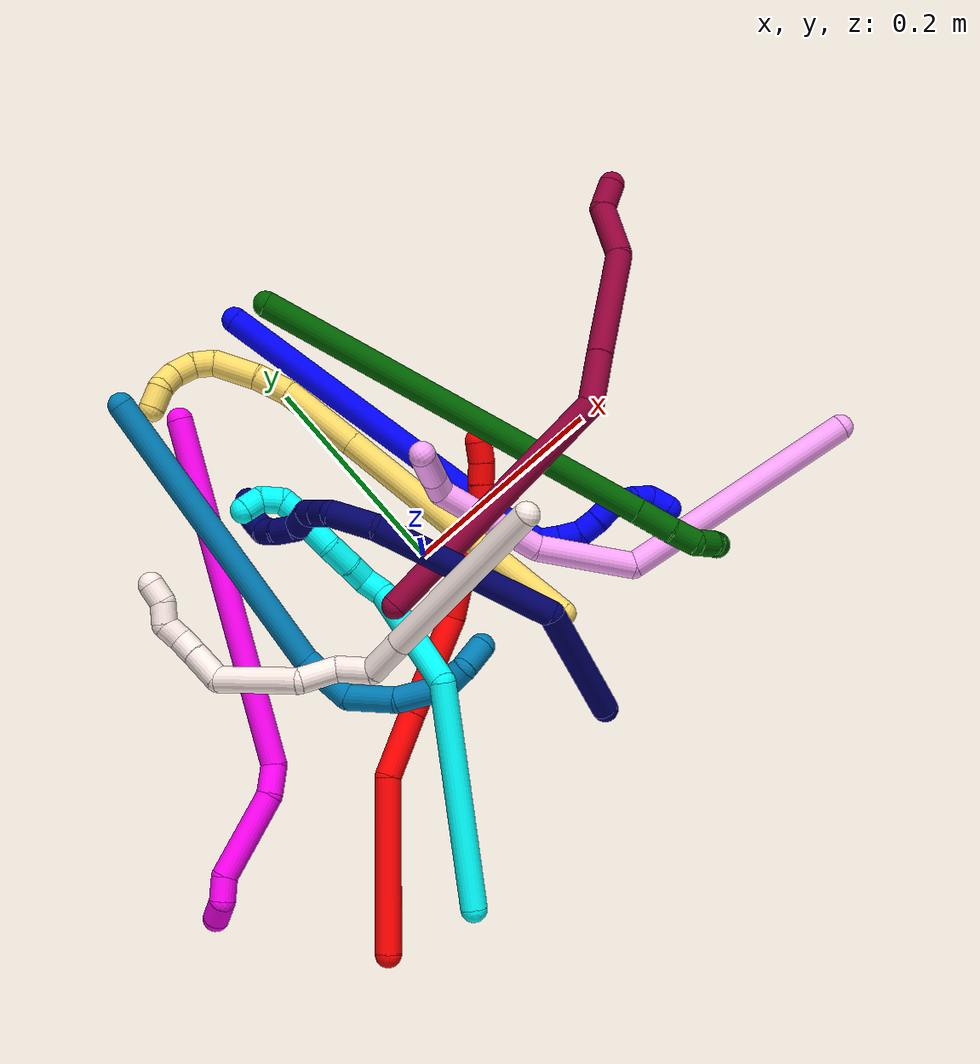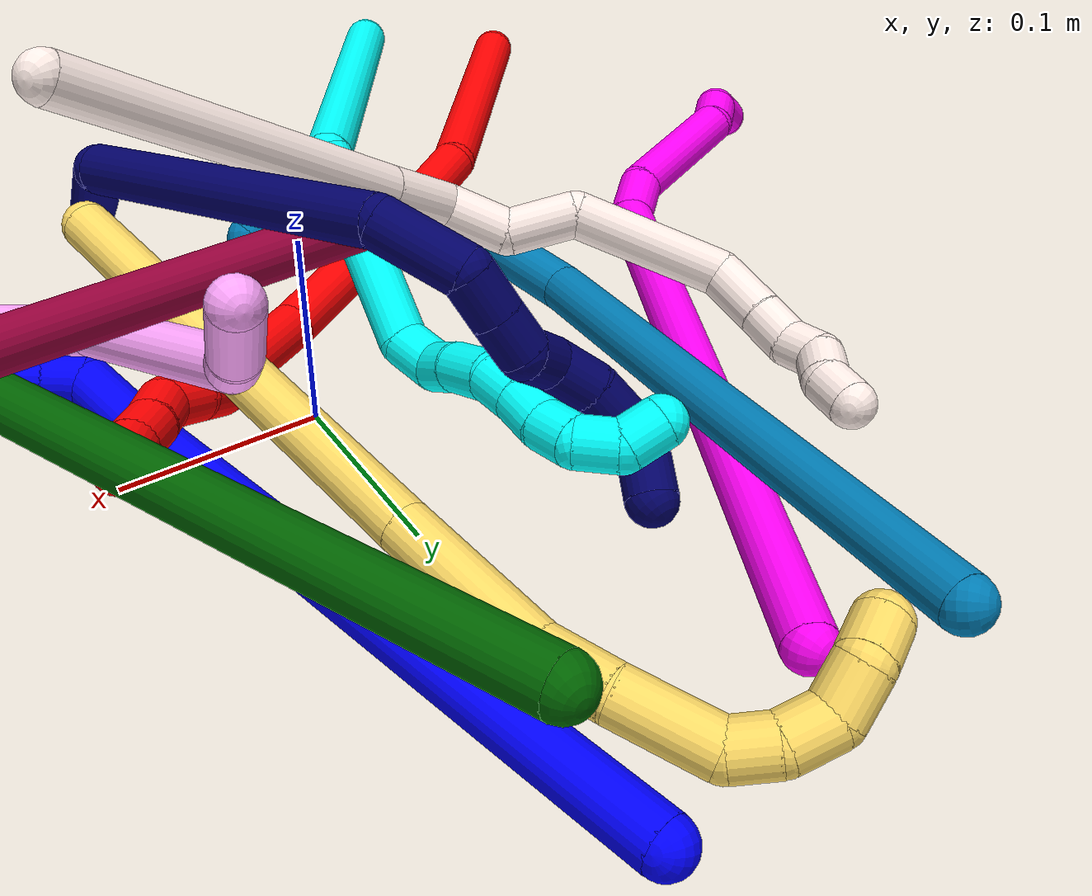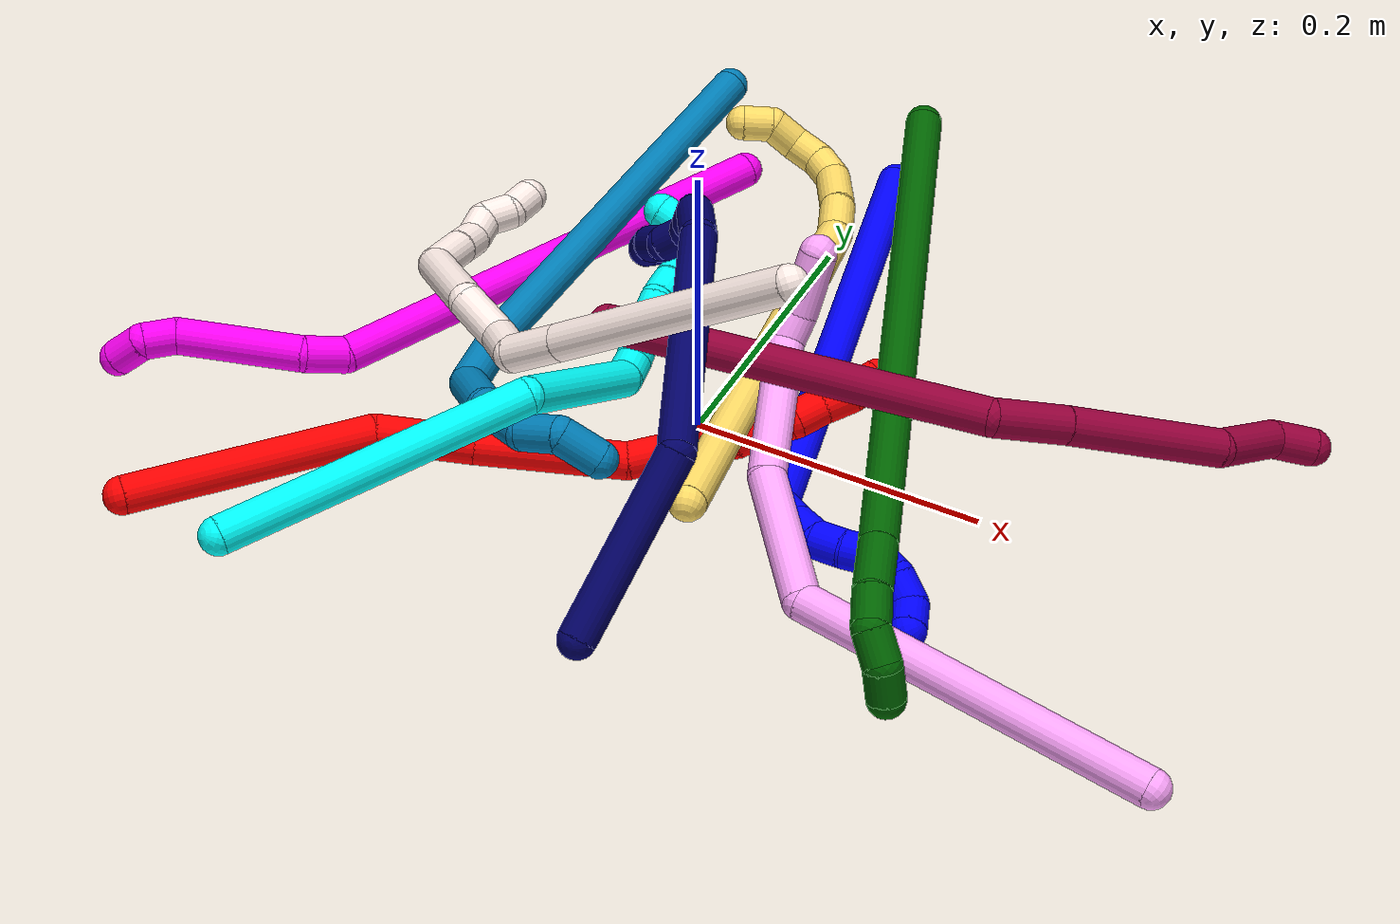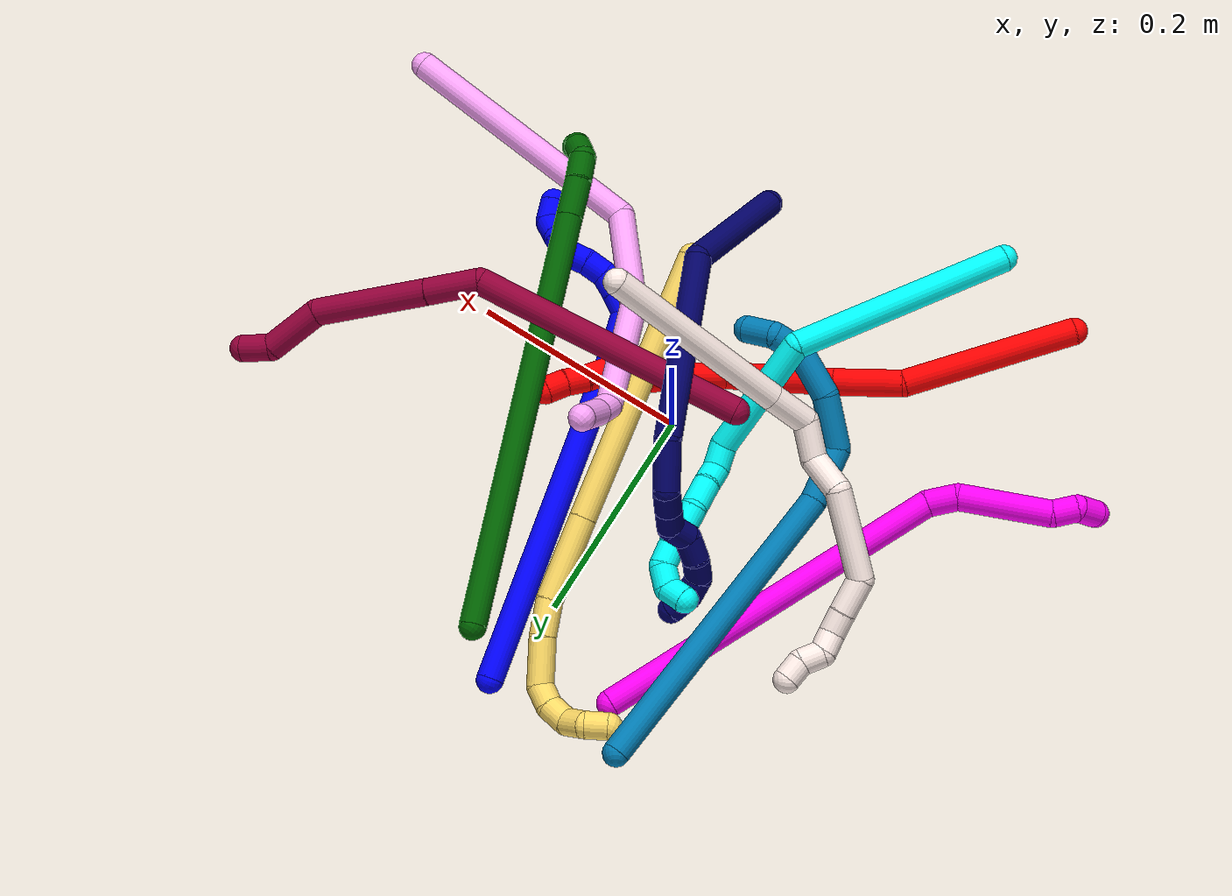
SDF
<sdf version="1.7">
 <world name="default">
  <plugin name="TubeGeneratorPlugin" filename="libtube_generator_plugin.so"/>
  <model name="photoneo_s_sensor">
   <static>1</static>
   <pose>0 0 2 1.57079 1.57079 3.14159</pose>
   <link name="link">
    <inertial><mass>0.1</mass></inertial>
    <sensor name="sensor" type="depth">
     <update_rate>30</update_rate>
     <camera>
      <horizontal_fov>1.22</horizontal_fov>
      <image><width>1920</width><height>1200</height><format>B8G8R8</format></image>
      <clip><near>0.1</near><far>4</far></clip>
      <depth_camera><output>points</output></depth_camera>
     </camera>
     <plugin name="camera_plugin" filename="libgazebo_ros_depth_camera.so">
      <baseline>0.2</baseline>
      <alwaysOn>1</alwaysOn>
      <updateRate>0.0</updateRate>
      <cameraName>camera_ir</cameraName>
      <imageTopicName>/camera/color/image_raw</imageTopicName>
      <cameraInfoTopicName>/camera/color/camera_info</cameraInfoTopicName>
      <depthImageTopicName>/camera/depth/image_raw</depthImageTopicName>
      <depthImageCameraInfoTopicName>/camera/depth/camera_info</depthImageCameraInfoTopicName>
      <pointCloudTopicName>/camera/depth/points</pointCloudTopicName>
      <frameName>fr_optical</frameName>
      <pointCloudCutoff>0.1</pointCloudCutoff>
      <pointCloudCutoffMax>2.0</pointCloudCutoffMax>
      <distortionK1>0</distortionK1>
      <distortionK2>0</distortionK2>
      <distortionK3>0</distortionK3>
      <distortionT1>0</distortionT1>
      <distortionT2>0</distortionT2>
      <CxPrime>0</CxPrime>
      <Cx>0</Cx>
      <Cy>0</Cy>
      <focalLength>0</focalLength>
      <hackBaseline>0</hackBaseline>
     </plugin>
    </sensor>
   </link>
  </model>
  <gravity>0 0 -9.8</gravity>
  <magnetic_field>6e-06 2.3e-05 -4.2e-05</magnetic_field>
  <atmosphere type="adiabatic"/>
  <physics name="default_physics" default="0" type="ode">
   <max_step_size>0.003</max_step_size>
   <real_time_factor>1</real_time_factor>
   <real_time_update_rate>1000</real_time_update_rate>
   <max_contacts>10000</max_contacts>
   <ode>
    <solver>
     <type>quick</type>
     <iters>100</iters>
     <sor>1.3</sor>
     <use_dynamic_moi_rescaling>0</use_dynamic_moi_rescaling>
    </solver>
    <constraints>
     <contact_max_correcting_vel>0</contact_max_correcting_vel>
     <contact_surface_layer>0.001</contact_surface_layer>
     <cfm>0</cfm>
     <erp>0.2</erp>
    </constraints>
   </ode>
  </physics>
  <scene><ambient>0.4 0.4 0.4 1</ambient><background>0.7 0.7 0.7 1</background><shadows>0</shadows></scene>
  <audio><device>default</device></audio>
  <spherical_coordinates>
   <surface_model>EARTH_WGS84</surface_model>
   <latitude_deg>0</latitude_deg>
   <longitude_deg>0</longitude_deg>
   <elevation>0</elevation>
   <heading_deg>0</heading_deg>
  </spherical_coordinates>
  <model name="bin">
   <static>1</static>
   <link name="bottom">
    <collision name="collision-bottom">
     <pose>0 0 -0.01 0 -0 0</pose>
     <geometry><box><size>0.8 0.6 0.02</size></box></geometry>
     <surface>
      <friction><ode><mu>100</mu><mu2>100</mu2></ode></friction>
      <contact><collide_bitmask>65535</collide_bitmask></contact>
     </surface>
    </collision>
   </link>
   <link name="west_wall">
    <collision name="collision-west_wall">
     <pose>-0.41 0 0.1 0 -0 0</pose>
     <geometry><box><size>0.02 0.6 0.2</size></box></geometry>
     <surface>
      <friction><ode><mu>100</mu><mu2>100</mu2></ode></friction>
      <contact><collide_bitmask>65535</collide_bitmask></contact>
     </surface>
    </collision>
   </link>
   <link name="east_wall">
    <collision name="collision-east_wall">
     <pose>0.41 0 0.1 0 -0 0</pose>
     <geometry><box><size>0.02 0.6 0.2</size></box></geometry>
     <surface>
      <friction><ode><mu>100</mu><mu2>100</mu2></ode></friction>
      <contact><collide_bitmask>65535</collide_bitmask></contact>
     </surface>
    </collision>
   </link>
   <link name="south_wall">
    <collision name="collision-south_wall">
     <pose>0 -0.31 0.1 0 -0 0</pose>
     <geometry><box><size>0.8 0.02 0.2</size></box></geometry>
     <surface>
      <friction><ode><mu>100</mu><mu2>100</mu2></ode></friction>
      <contact><collide_bitmask>65535</collide_bitmask></contact>
     </surface>
    </collision>
   </link>
   <link name="north_wall">
    <collision name="collision-north_wall">
     <pose>0 0.31 0.1 0 -0 0</pose>
     <geometry><box><size>0.8 0.02 0.2</size></box></geometry>
     <surface>
      <friction><ode><mu>100</mu><mu2>100</mu2></ode></friction>
      <contact><collide_bitmask>65535</collide_bitmask></contact>
     </surface>
    </collision>
   </link>
  </model>
  <model name="1">
   <static>0</static>
   <link name="1">
    <collision name="collision-cylinder-e_1_1_4">
     <pose>0.009804 -0.155916 0.025654 1.40772 0.061969 0.052611</pose>
     <geometry><cylinder><radius>0.0125</radius><length>0.316633</length></cylinder></geometry>
     <surface>
      <friction><ode><mu>1.16</mu><mu2>1.16</mu2><slip1>0</slip1><slip2>0</slip2></ode></friction>
      <contact><ode><kp>1e+06</kp><kd>1</kd><max_vel>0</max_vel><min_depth>0.001</min_depth></ode></contact>
     </surface>
    </collision>
    <visual name="visual-cylinder-e_1_1_4">
     <pose>0.009804 -0.155916 0.025654 1.40772 0.061969 0.052611</pose>
     <geometry><cylinder><radius>0.0125</radius><length>0.316633</length></cylinder></geometry>
     <material><ambient>0 0 1 1</ambient></material>
    </visual>
    <collision name="collision-cylinder-e_2_4_5">
     <pose>0.023618 -0.333019 0.052096 1.53367 0.186908 0.180133</pose>
     <geometry><cylinder><radius>0.0125</radius><length>0.043155</length></cylinder></geometry>
     <surface>
      <friction><ode><mu>1.16</mu><mu2>1.16</mu2><slip1>0</slip1><slip2>0</slip2></ode></friction>
      <contact><ode><kp>1e+06</kp><kd>1</kd><max_vel>0</max_vel><min_depth>0.001</min_depth></ode></contact>
     </surface>
    </collision>
    <visual name="visual-cylinder-e_2_4_5">
     <pose>0.023618 -0.333019 0.052096 1.53367 0.186908 0.180133</pose>
     <geometry><cylinder><radius>0.0125</radius><length>0.043155</length></cylinder></geometry>
     <material><ambient>0 0 1 1</ambient></material>
    </visual>
    <collision name="collision-cylinder-e_3_5_6">
     <pose>0.024657 -0.362366 0.047778 2.12976 -0.299432 -0.531669</pose>
     <geometry><cylinder><radius>0.0125</radius><length>0.020146</length></cylinder></geometry>
     <surface>
      <friction><ode><mu>1.16</mu><mu2>1.16</mu2><slip1>0</slip1><slip2>0</slip2></ode></friction>
      <contact><ode><kp>1e+06</kp><kd>1</kd><max_vel>0</max_vel><min_depth>0.001</min_depth></ode></contact>
     </surface>
    </collision>
    <visual name="visual-cylinder-e_3_5_6">
     <pose>0.024657 -0.362366 0.047778 2.12976 -0.299432 -0.531669</pose>
     <geometry><cylinder><radius>0.0125</radius><length>0.020146</length></cylinder></geometry>
     <material><ambient>0 0 1 1</ambient></material>
    </visual>
    <collision name="collision-cylinder-e_4_6_7">
     <pose>0.018707 -0.378202 0.036944 2.21209 -0.301434 -0.588231</pose>
     <geometry><cylinder><radius>0.0125</radius><length>0.020063</length></cylinder></geometry>
     <surface>
      <friction><ode><mu>1.16</mu><mu2>1.16</mu2><slip1>0</slip1><slip2>0</slip2></ode></friction>
      <contact><ode><kp>1e+06</kp><kd>1</kd><max_vel>0</max_vel><min_depth>0.001</min_depth></ode></contact>
     </surface>
    </collision>
    <visual name="visual-cylinder-e_4_6_7">
     <pose>0.018707 -0.378202 0.036944 2.21209 -0.301434 -0.588231</pose>
     <geometry><cylinder><radius>0.0125</radius><length>0.020063</length></cylinder></geometry>
     <material><ambient>0 0 1 1</ambient></material>
    </visual>
    <collision name="collision-cylinder-e_5_7_8">
     <pose>0.011252 -0.390191 0.023378 2.63835 -0.464069 -1.4866</pose>
     <geometry><cylinder><radius>0.0125</radius><length>0.020002</length></cylinder></geometry>
     <surface>
      <friction><ode><mu>1.16</mu><mu2>1.16</mu2><slip1>0</slip1><slip2>0</slip2></ode></friction>
      <contact><ode><kp>1e+06</kp><kd>1</kd><max_vel>0</max_vel><min_depth>0.001</min_depth></ode></contact>
     </surface>
    </collision>
    <visual name="visual-cylinder-e_5_7_8">
     <pose>0.011252 -0.390191 0.023378 2.63835 -0.464069 -1.4866</pose>
     <geometry><cylinder><radius>0.0125</radius><length>0.020002</length></cylinder></geometry>
     <material><ambient>0 0 1 1</ambient></material>
    </visual>
    <collision name="collision-cylinder-e_6_8_9">
     <pose>0.001539 -0.397184 0.007456 2.82168 -0.55113 -2.1046</pose>
     <geometry><cylinder><radius>0.0125</radius><length>0.020001</length></cylinder></geometry>
     <surface>
      <friction><ode><mu>1.16</mu><mu2>1.16</mu2><slip1>0</slip1><slip2>0</slip2></ode></friction>
      <contact><ode><kp>1e+06</kp><kd>1</kd><max_vel>0</max_vel><min_depth>0.001</min_depth></ode></contact>
     </surface>
    </collision>
    <visual name="visual-cylinder-e_6_8_9">
     <pose>0.001539 -0.397184 0.007456 2.82168 -0.55113 -2.1046</pose>
     <geometry><cylinder><radius>0.0125</radius><length>0.020001</length></cylinder></geometry>
     <material><ambient>0 0 1 1</ambient></material>
    </visual>
    <collision name="collision-cylinder-e_7_9_10">
     <pose>-0.008178 -0.407282 -0.005619 2.16267 -0.464552 -0.835798</pose>
     <geometry><cylinder><radius>0.0125</radius><length>0.02</length></cylinder></geometry>
     <surface>
      <friction><ode><mu>1.16</mu><mu2>1.16</mu2><slip1>0</slip1><slip2>0</slip2></ode></friction>
      <contact><ode><kp>1e+06</kp><kd>1</kd><max_vel>0</max_vel><min_depth>0.001</min_depth></ode></contact>
     </surface>
    </collision>
    <visual name="visual-cylinder-e_7_9_10">
     <pose>-0.008178 -0.407282 -0.005619 2.16267 -0.464552 -0.835798</pose>
     <geometry><cylinder><radius>0.0125</radius><length>0.02</length></cylinder></geometry>
     <material><ambient>0 0 1 1</ambient></material>
    </visual>
    <collision name="collision-cylinder-e_8_10_11">
     <pose>-0.019474 -0.421891 -0.011972 1.75847 -0.749908 -0.887469</pose>
     <geometry><cylinder><radius>0.0125</radius><length>0.02</length></cylinder></geometry>
     <surface>
      <friction><ode><mu>1.16</mu><mu2>1.16</mu2><slip1>0</slip1><slip2>0</slip2></ode></friction>
      <contact><ode><kp>1e+06</kp><kd>1</kd><max_vel>0</max_vel><min_depth>0.001</min_depth></ode></contact>
     </surface>
    </collision>
    <visual name="visual-cylinder-e_8_10_11">
     <pose>-0.019474 -0.421891 -0.011972 1.75847 -0.749908 -0.887469</pose>
     <geometry><cylinder><radius>0.0125</radius><length>0.02</length></cylinder></geometry>
     <material><ambient>0 0 1 1</ambient></material>
    </visual>
    <collision name="collision-cylinder-e_9_11_2">
     <pose>-0.026848 -0.439032 -0.012536 1.49042 -0.055934 -0.051612</pose>
     <geometry><cylinder><radius>0.0125</radius><length>0.02</length></cylinder></geometry>
     <surface>
      <friction><ode><mu>1.16</mu><mu2>1.16</mu2><slip1>0</slip1><slip2>0</slip2></ode></friction>
      <contact><ode><kp>1e+06</kp><kd>1</kd><max_vel>0</max_vel><min_depth>0.001</min_depth></ode></contact>
     </surface>
    </collision>
    <visual name="visual-cylinder-e_9_11_2">
     <pose>-0.026848 -0.439032 -0.012536 1.49042 -0.055934 -0.051612</pose>
     <geometry><cylinder><radius>0.0125</radius><length>0.02</length></cylinder></geometry>
     <material><ambient>0 0 1 1</ambient></material>
    </visual>
    <collision name="collision-sphere-2">
     <pose>-0.027408 -0.448984 -0.011734 0 -0 0</pose>
     <geometry><sphere><radius>0.0125</radius></sphere></geometry>
     <surface>
      <friction><ode><mu>1.16</mu><mu2>1.16</mu2><slip1>0</slip1><slip2>0</slip2></ode></friction>
      <contact><ode><kp>1e+06</kp><kd>1</kd><max_vel>0</max_vel><min_depth>0.001</min_depth></ode></contact>
     </surface>
    </collision>
    <visual name="visual-sphere-2">
     <pose>-0.027408 -0.448984 -0.011734 0 -0 0</pose>
     <geometry><sphere><radius>0.0125</radius></sphere></geometry>
     <material><ambient>0 0 1 1</ambient></material>
    </visual>
    <collision name="collision-sphere-11">
     <pose>-0.026289 -0.42908 -0.013338 0 -0 0</pose>
     <geometry><sphere><radius>0.0125</radius></sphere></geometry>
     <surface>
      <friction><ode><mu>1.16</mu><mu2>1.16</mu2><slip1>0</slip1><slip2>0</slip2></ode></friction>
      <contact><ode><kp>1e+06</kp><kd>1</kd><max_vel>0</max_vel><min_depth>0.001</min_depth></ode></contact>
     </surface>
    </collision>
    <visual name="visual-sphere-11">
     <pose>-0.026289 -0.42908 -0.013338 0 -0 0</pose>
     <geometry><sphere><radius>0.0125</radius></sphere></geometry>
     <material><ambient>0 0 1 1</ambient></material>
    </visual>
    <collision name="collision-sphere-10">
     <pose>-0.012658 -0.414702 -0.010607 0 -0 0</pose>
     <geometry><sphere><radius>0.0125</radius></sphere></geometry>
     <surface>
      <friction><ode><mu>1.16</mu><mu2>1.16</mu2><slip1>0</slip1><slip2>0</slip2></ode></friction>
      <contact><ode><kp>1e+06</kp><kd>1</kd><max_vel>0</max_vel><min_depth>0.001</min_depth></ode></contact>
     </surface>
    </collision>
    <visual name="visual-sphere-10">
     <pose>-0.012658 -0.414702 -0.010607 0 -0 0</pose>
     <geometry><sphere><radius>0.0125</radius></sphere></geometry>
     <material><ambient>0 0 1 1</ambient></material>
    </visual>
    <collision name="collision-sphere-9">
     <pose>-0.003697 -0.399863 -0.000631 0 -0 0</pose>
     <geometry><sphere><radius>0.0125</radius></sphere></geometry>
     <surface>
      <friction><ode><mu>1.16</mu><mu2>1.16</mu2><slip1>0</slip1><slip2>0</slip2></ode></friction>
      <contact><ode><kp>1e+06</kp><kd>1</kd><max_vel>0</max_vel><min_depth>0.001</min_depth></ode></contact>
     </surface>
    </collision>
    <visual name="visual-sphere-9">
     <pose>-0.003697 -0.399863 -0.000631 0 -0 0</pose>
     <geometry><sphere><radius>0.0125</radius></sphere></geometry>
     <material><ambient>0 0 1 1</ambient></material>
    </visual>
    <collision name="collision-sphere-4">
     <pose>0.019609 -0.311832 0.051309 0 -0 0</pose>
     <geometry><sphere><radius>0.0125</radius></sphere></geometry>
     <surface>
      <friction><ode><mu>1.16</mu><mu2>1.16</mu2><slip1>0</slip1><slip2>0</slip2></ode></friction>
      <contact><ode><kp>1e+06</kp><kd>1</kd><max_vel>0</max_vel><min_depth>0.001</min_depth></ode></contact>
     </surface>
    </collision>
    <visual name="visual-sphere-4">
     <pose>0.019609 -0.311832 0.051309 0 -0 0</pose>
     <geometry><sphere><radius>0.0125</radius></sphere></geometry>
     <material><ambient>0 0 1 1</ambient></material>
    </visual>
    <collision name="collision-sphere-1">
     <geometry><sphere><radius>0.0125</radius></sphere></geometry>
     <surface>
      <friction><ode><mu>1.16</mu><mu2>1.16</mu2><slip1>0</slip1><slip2>0</slip2></ode></friction>
      <contact><ode><kp>1e+06</kp><kd>1</kd><max_vel>0</max_vel><min_depth>0.001</min_depth></ode></contact>
     </surface>
    </collision>
    <visual name="visual-sphere-1">
     <geometry><sphere><radius>0.0125</radius></sphere></geometry>
     <material><ambient>0 0 1 1</ambient></material>
    </visual>
    <collision name="collision-sphere-8">
     <pose>0.006776 -0.394504 0.015544 0 -0 0</pose>
     <geometry><sphere><radius>0.0125</radius></sphere></geometry>
     <surface>
      <friction><ode><mu>1.16</mu><mu2>1.16</mu2><slip1>0</slip1><slip2>0</slip2></ode></friction>
      <contact><ode><kp>1e+06</kp><kd>1</kd><max_vel>0</max_vel><min_depth>0.001</min_depth></ode></contact>
     </surface>
    </collision>
    <visual name="visual-sphere-8">
     <pose>0.006776 -0.394504 0.015544 0 -0 0</pose>
     <geometry><sphere><radius>0.0125</radius></sphere></geometry>
     <material><ambient>0 0 1 1</ambient></material>
    </visual>
    <collision name="collision-sphere-5">
     <pose>0.027628 -0.354206 0.052882 0 -0 0</pose>
     <geometry><sphere><radius>0.0125</radius></sphere></geometry>
     <surface>
      <friction><ode><mu>1.16</mu><mu2>1.16</mu2><slip1>0</slip1><slip2>0</slip2></ode></friction>
      <contact><ode><kp>1e+06</kp><kd>1</kd><max_vel>0</max_vel><min_depth>0.001</min_depth></ode></contact>
     </surface>
    </collision>
    <visual name="visual-sphere-5">
     <pose>0.027628 -0.354206 0.052882 0 -0 0</pose>
     <geometry><sphere><radius>0.0125</radius></sphere></geometry>
     <material><ambient>0 0 1 1</ambient></material>
    </visual>
    <collision name="collision-sphere-6">
     <pose>0.021685 -0.370526 0.042674 0 -0 0</pose>
     <geometry><sphere><radius>0.0125</radius></sphere></geometry>
     <surface>
      <friction><ode><mu>1.16</mu><mu2>1.16</mu2><slip1>0</slip1><slip2>0</slip2></ode></friction>
      <contact><ode><kp>1e+06</kp><kd>1</kd><max_vel>0</max_vel><min_depth>0.001</min_depth></ode></contact>
     </surface>
    </collision>
    <visual name="visual-sphere-6">
     <pose>0.021685 -0.370526 0.042674 0 -0 0</pose>
     <geometry><sphere><radius>0.0125</radius></sphere></geometry>
     <material><ambient>0 0 1 1</ambient></material>
    </visual>
    <collision name="collision-sphere-7">
     <pose>0.015729 -0.385878 0.031213 0 -0 0</pose>
     <geometry><sphere><radius>0.0125</radius></sphere></geometry>
     <surface>
      <friction><ode><mu>1.16</mu><mu2>1.16</mu2><slip1>0</slip1><slip2>0</slip2></ode></friction>
      <contact><ode><kp>1e+06</kp><kd>1</kd><max_vel>0</max_vel><min_depth>0.001</min_depth></ode></contact>
     </surface>
    </collision>
    <visual name="visual-sphere-7">
     <pose>0.015729 -0.385878 0.031213 0 -0 0</pose>
     <geometry><sphere><radius>0.0125</radius></sphere></geometry>
     <material><ambient>0 0 1 1</ambient></material>
    </visual>
    <inertial>
     <pose>0.008323 -0.239481 0.024178 0 -0 0</pose>
     <mass>0.5</mass>
     <inertia>
      <ixx>0.002795</ixx>
      <ixy>0</ixy>
      <ixz>0</ixz>
      <iyy>0.000541</iyy>
      <iyz>0</iyz>
      <izz>0.002469</izz>
     </inertia>
    </inertial>
   </link>
   <pose>0.011131 0.28751 0.011498 -3.07125 -0.987084 -2.81303</pose>
  </model>
  <model name="2">
   <static>0</static>
   <link name="2">
    <collision name="collision-cylinder-e_1_1_4">
     <pose>0.081143 0.007715 -0.00153 -1.76662 1.47417 -1.67094</pose>
     <geometry><cylinder><radius>0.0125</radius><length>0.163047</length></cylinder></geometry>
     <surface>
      <friction><ode><mu>1.16</mu><mu2>1.16</mu2><slip1>0</slip1><slip2>0</slip2></ode></friction>
      <contact><ode><kp>1e+06</kp><kd>1</kd><max_vel>0</max_vel><min_depth>0.001</min_depth></ode></contact>
     </surface>
    </collision>
    <visual name="visual-cylinder-e_1_1_4">
     <pose>0.081143 0.007715 -0.00153 -1.76662 1.47417 -1.67094</pose>
     <geometry><cylinder><radius>0.0125</radius><length>0.163047</length></cylinder></geometry>
     <material><ambient>1 0 0 1</ambient></material>
    </visual>
    <collision name="collision-cylinder-e_2_4_5">
     <pose>0.191295 0.022185 0.008252 -0.538303 1.14444 -0.351676</pose>
     <geometry><cylinder><radius>0.0125</radius><length>0.063721</length></cylinder></geometry>
     <surface>
      <friction><ode><mu>1.16</mu><mu2>1.16</mu2><slip1>0</slip1><slip2>0</slip2></ode></friction>
      <contact><ode><kp>1e+06</kp><kd>1</kd><max_vel>0</max_vel><min_depth>0.001</min_depth></ode></contact>
     </surface>
    </collision>
    <visual name="visual-cylinder-e_2_4_5">
     <pose>0.191295 0.022185 0.008252 -0.538303 1.14444 -0.351676</pose>
     <geometry><cylinder><radius>0.0125</radius><length>0.063721</length></cylinder></geometry>
     <material><ambient>1 0 0 1</ambient></material>
    </visual>
    <collision name="collision-cylinder-e_3_5_6">
     <pose>0.265056 0.042373 0.036248 -0.677897 1.1244 -0.437136</pose>
     <geometry><cylinder><radius>0.0125</radius><length>0.099229</length></cylinder></geometry>
     <surface>
      <friction><ode><mu>1.16</mu><mu2>1.16</mu2><slip1>0</slip1><slip2>0</slip2></ode></friction>
      <contact><ode><kp>1e+06</kp><kd>1</kd><max_vel>0</max_vel><min_depth>0.001</min_depth></ode></contact>
     </surface>
    </collision>
    <visual name="visual-cylinder-e_3_5_6">
     <pose>0.265056 0.042373 0.036248 -0.677897 1.1244 -0.437136</pose>
     <geometry><cylinder><radius>0.0125</radius><length>0.099229</length></cylinder></geometry>
     <material><ambient>1 0 0 1</ambient></material>
    </visual>
    <collision name="collision-cylinder-e_4_6_7">
     <pose>0.332542 0.064778 0.053466 -1.51125 1.19434 -1.13956</pose>
     <geometry><cylinder><radius>0.0125</radius><length>0.048892</length></cylinder></geometry>
     <surface>
      <friction><ode><mu>1.16</mu><mu2>1.16</mu2><slip1>0</slip1><slip2>0</slip2></ode></friction>
      <contact><ode><kp>1e+06</kp><kd>1</kd><max_vel>0</max_vel><min_depth>0.001</min_depth></ode></contact>
     </surface>
    </collision>
    <visual name="visual-cylinder-e_4_6_7">
     <pose>0.332542 0.064778 0.053466 -1.51125 1.19434 -1.13956</pose>
     <geometry><cylinder><radius>0.0125</radius><length>0.048892</length></cylinder></geometry>
     <material><ambient>1 0 0 1</ambient></material>
    </visual>
    <collision name="collision-cylinder-e_5_7_8">
     <pose>0.366141 0.076689 0.055352 -1.13994 1.28134 -0.891567</pose>
     <geometry><cylinder><radius>0.0125</radius><length>0.022673</length></cylinder></geometry>
     <surface>
      <friction><ode><mu>1.16</mu><mu2>1.16</mu2><slip1>0</slip1><slip2>0</slip2></ode></friction>
      <contact><ode><kp>1e+06</kp><kd>1</kd><max_vel>0</max_vel><min_depth>0.001</min_depth></ode></contact>
     </surface>
    </collision>
    <visual name="visual-cylinder-e_5_7_8">
     <pose>0.366141 0.076689 0.055352 -1.13994 1.28134 -0.891567</pose>
     <geometry><cylinder><radius>0.0125</radius><length>0.022673</length></cylinder></geometry>
     <material><ambient>1 0 0 1</ambient></material>
    </visual>
    <collision name="collision-cylinder-e_6_8_9">
     <pose>0.385053 0.08559 0.054887 -1.86666 0.911795 -1.16965</pose>
     <geometry><cylinder><radius>0.0125</radius><length>0.020356</length></cylinder></geometry>
     <surface>
      <friction><ode><mu>1.16</mu><mu2>1.16</mu2><slip1>0</slip1><slip2>0</slip2></ode></friction>
      <contact><ode><kp>1e+06</kp><kd>1</kd><max_vel>0</max_vel><min_depth>0.001</min_depth></ode></contact>
     </surface>
    </collision>
    <visual name="visual-cylinder-e_6_8_9">
     <pose>0.385053 0.08559 0.054887 -1.86666 0.911795 -1.16965</pose>
     <geometry><cylinder><radius>0.0125</radius><length>0.020356</length></cylinder></geometry>
     <material><ambient>1 0 0 1</ambient></material>
    </visual>
    <collision name="collision-cylinder-e_7_9_10">
     <pose>0.401129 0.09833 0.053507 -1.5064 0.868609 -0.82044</pose>
     <geometry><cylinder><radius>0.0125</radius><length>0.021034</length></cylinder></geometry>
     <surface>
      <friction><ode><mu>1.16</mu><mu2>1.16</mu2><slip1>0</slip1><slip2>0</slip2></ode></friction>
      <contact><ode><kp>1e+06</kp><kd>1</kd><max_vel>0</max_vel><min_depth>0.001</min_depth></ode></contact>
     </surface>
    </collision>
    <visual name="visual-cylinder-e_7_9_10">
     <pose>0.401129 0.09833 0.053507 -1.5064 0.868609 -0.82044</pose>
     <geometry><cylinder><radius>0.0125</radius><length>0.021034</length></cylinder></geometry>
     <material><ambient>1 0 0 1</ambient></material>
    </visual>
    <collision name="collision-cylinder-e_8_10_11">
     <pose>0.418949 0.107012 0.051618 -2.45584 1.27298 -2.2417</pose>
     <geometry><cylinder><radius>0.0125</radius><length>0.020485</length></cylinder></geometry>
     <surface>
      <friction><ode><mu>1.16</mu><mu2>1.16</mu2><slip1>0</slip1><slip2>0</slip2></ode></friction>
      <contact><ode><kp>1e+06</kp><kd>1</kd><max_vel>0</max_vel><min_depth>0.001</min_depth></ode></contact>
     </surface>
    </collision>
    <visual name="visual-cylinder-e_8_10_11">
     <pose>0.418949 0.107012 0.051618 -2.45584 1.27298 -2.2417</pose>
     <geometry><cylinder><radius>0.0125</radius><length>0.020485</length></cylinder></geometry>
     <material><ambient>1 0 0 1</ambient></material>
    </visual>
    <collision name="collision-cylinder-e_9_11_12">
     <pose>0.438414 0.111728 0.047778 -2.06451 1.25186 -1.76025</pose>
     <geometry><cylinder><radius>0.0125</radius><length>0.020373</length></cylinder></geometry>
     <surface>
      <friction><ode><mu>1.16</mu><mu2>1.16</mu2><slip1>0</slip1><slip2>0</slip2></ode></friction>
      <contact><ode><kp>1e+06</kp><kd>1</kd><max_vel>0</max_vel><min_depth>0.001</min_depth></ode></contact>
     </surface>
    </collision>
    <visual name="visual-cylinder-e_9_11_12">
     <pose>0.438414 0.111728 0.047778 -2.06451 1.25186 -1.76025</pose>
     <geometry><cylinder><radius>0.0125</radius><length>0.020373</length></cylinder></geometry>
     <material><ambient>1 0 0 1</ambient></material>
    </visual>
    <collision name="collision-cylinder-e_10_12_2">
     <pose>0.457578 0.11625 0.043281 -2.62137 1.22323 -2.4162</pose>
     <geometry><cylinder><radius>0.0125</radius><length>0.020191</length></cylinder></geometry>
     <surface>
      <friction><ode><mu>1.16</mu><mu2>1.16</mu2><slip1>0</slip1><slip2>0</slip2></ode></friction>
      <contact><ode><kp>1e+06</kp><kd>1</kd><max_vel>0</max_vel><min_depth>0.001</min_depth></ode></contact>
     </surface>
    </collision>
    <visual name="visual-cylinder-e_10_12_2">
     <pose>0.457578 0.11625 0.043281 -2.62137 1.22323 -2.4162</pose>
     <geometry><cylinder><radius>0.0125</radius><length>0.020191</length></cylinder></geometry>
     <material><ambient>1 0 0 1</ambient></material>
    </visual>
    <collision name="collision-sphere-2">
     <pose>0.46707 0.117959 0.040297 0 -0 0</pose>
     <geometry><sphere><radius>0.0125</radius></sphere></geometry>
     <surface>
      <friction><ode><mu>1.16</mu><mu2>1.16</mu2><slip1>0</slip1><slip2>0</slip2></ode></friction>
      <contact><ode><kp>1e+06</kp><kd>1</kd><max_vel>0</max_vel><min_depth>0.001</min_depth></ode></contact>
     </surface>
    </collision>
    <visual name="visual-sphere-2">
     <pose>0.46707 0.117959 0.040297 0 -0 0</pose>
     <geometry><sphere><radius>0.0125</radius></sphere></geometry>
     <material><ambient>1 0 0 1</ambient></material>
    </visual>
    <collision name="collision-sphere-12">
     <pose>0.448086 0.114541 0.046264 0 -0 0</pose>
     <geometry><sphere><radius>0.0125</radius></sphere></geometry>
     <surface>
      <friction><ode><mu>1.16</mu><mu2>1.16</mu2><slip1>0</slip1><slip2>0</slip2></ode></friction>
      <contact><ode><kp>1e+06</kp><kd>1</kd><max_vel>0</max_vel><min_depth>0.001</min_depth></ode></contact>
     </surface>
    </collision>
    <visual name="visual-sphere-12">
     <pose>0.448086 0.114541 0.046264 0 -0 0</pose>
     <geometry><sphere><radius>0.0125</radius></sphere></geometry>
     <material><ambient>1 0 0 1</ambient></material>
    </visual>
    <collision name="collision-sphere-11">
     <pose>0.428741 0.108915 0.049292 0 -0 0</pose>
     <geometry><sphere><radius>0.0125</radius></sphere></geometry>
     <surface>
      <friction><ode><mu>1.16</mu><mu2>1.16</mu2><slip1>0</slip1><slip2>0</slip2></ode></friction>
      <contact><ode><kp>1e+06</kp><kd>1</kd><max_vel>0</max_vel><min_depth>0.001</min_depth></ode></contact>
     </surface>
    </collision>
    <visual name="visual-sphere-11">
     <pose>0.428741 0.108915 0.049292 0 -0 0</pose>
     <geometry><sphere><radius>0.0125</radius></sphere></geometry>
     <material><ambient>1 0 0 1</ambient></material>
    </visual>
    <collision name="collision-sphere-10">
     <pose>0.409157 0.105109 0.053944 0 -0 0</pose>
     <geometry><sphere><radius>0.0125</radius></sphere></geometry>
     <surface>
      <friction><ode><mu>1.16</mu><mu2>1.16</mu2><slip1>0</slip1><slip2>0</slip2></ode></friction>
      <contact><ode><kp>1e+06</kp><kd>1</kd><max_vel>0</max_vel><min_depth>0.001</min_depth></ode></contact>
     </surface>
    </collision>
    <visual name="visual-sphere-10">
     <pose>0.409157 0.105109 0.053944 0 -0 0</pose>
     <geometry><sphere><radius>0.0125</radius></sphere></geometry>
     <material><ambient>1 0 0 1</ambient></material>
    </visual>
    <collision name="collision-sphere-9">
     <pose>0.3931 0.091552 0.05307 0 -0 0</pose>
     <geometry><sphere><radius>0.0125</radius></sphere></geometry>
     <surface>
      <friction><ode><mu>1.16</mu><mu2>1.16</mu2><slip1>0</slip1><slip2>0</slip2></ode></friction>
      <contact><ode><kp>1e+06</kp><kd>1</kd><max_vel>0</max_vel><min_depth>0.001</min_depth></ode></contact>
     </surface>
    </collision>
    <visual name="visual-sphere-9">
     <pose>0.3931 0.091552 0.05307 0 -0 0</pose>
     <geometry><sphere><radius>0.0125</radius></sphere></geometry>
     <material><ambient>1 0 0 1</ambient></material>
    </visual>
    <collision name="collision-sphere-4">
     <pose>0.162286 0.01543 -0.003061 0 -0 0</pose>
     <geometry><sphere><radius>0.0125</radius></sphere></geometry>
     <surface>
      <friction><ode><mu>1.16</mu><mu2>1.16</mu2><slip1>0</slip1><slip2>0</slip2></ode></friction>
      <contact><ode><kp>1e+06</kp><kd>1</kd><max_vel>0</max_vel><min_depth>0.001</min_depth></ode></contact>
     </surface>
    </collision>
    <visual name="visual-sphere-4">
     <pose>0.162286 0.01543 -0.003061 0 -0 0</pose>
     <geometry><sphere><radius>0.0125</radius></sphere></geometry>
     <material><ambient>1 0 0 1</ambient></material>
    </visual>
    <collision name="collision-sphere-1">
     <geometry><sphere><radius>0.0125</radius></sphere></geometry>
     <surface>
      <friction><ode><mu>1.16</mu><mu2>1.16</mu2><slip1>0</slip1><slip2>0</slip2></ode></friction>
      <contact><ode><kp>1e+06</kp><kd>1</kd><max_vel>0</max_vel><min_depth>0.001</min_depth></ode></contact>
     </surface>
    </collision>
    <visual name="visual-sphere-1">
     <geometry><sphere><radius>0.0125</radius></sphere></geometry>
     <material><ambient>1 0 0 1</ambient></material>
    </visual>
    <collision name="collision-sphere-8">
     <pose>0.377006 0.079629 0.056704 0 -0 0</pose>
     <geometry><sphere><radius>0.0125</radius></sphere></geometry>
     <surface>
      <friction><ode><mu>1.16</mu><mu2>1.16</mu2><slip1>0</slip1><slip2>0</slip2></ode></friction>
      <contact><ode><kp>1e+06</kp><kd>1</kd><max_vel>0</max_vel><min_depth>0.001</min_depth></ode></contact>
     </surface>
    </collision>
    <visual name="visual-sphere-8">
     <pose>0.377006 0.079629 0.056704 0 -0 0</pose>
     <geometry><sphere><radius>0.0125</radius></sphere></geometry>
     <material><ambient>1 0 0 1</ambient></material>
    </visual>
    <collision name="collision-sphere-5">
     <pose>0.220303 0.02894 0.019565 0 -0 0</pose>
     <geometry><sphere><radius>0.0125</radius></sphere></geometry>
     <surface>
      <friction><ode><mu>1.16</mu><mu2>1.16</mu2><slip1>0</slip1><slip2>0</slip2></ode></friction>
      <contact><ode><kp>1e+06</kp><kd>1</kd><max_vel>0</max_vel><min_depth>0.001</min_depth></ode></contact>
     </surface>
    </collision>
    <visual name="visual-sphere-5">
     <pose>0.220303 0.02894 0.019565 0 -0 0</pose>
     <geometry><sphere><radius>0.0125</radius></sphere></geometry>
     <material><ambient>1 0 0 1</ambient></material>
    </visual>
    <collision name="collision-sphere-6">
     <pose>0.309808 0.055806 0.052931 0 -0 0</pose>
     <geometry><sphere><radius>0.0125</radius></sphere></geometry>
     <surface>
      <friction><ode><mu>1.16</mu><mu2>1.16</mu2><slip1>0</slip1><slip2>0</slip2></ode></friction>
      <contact><ode><kp>1e+06</kp><kd>1</kd><max_vel>0</max_vel><min_depth>0.001</min_depth></ode></contact>
     </surface>
    </collision>
    <visual name="visual-sphere-6">
     <pose>0.309808 0.055806 0.052931 0 -0 0</pose>
     <geometry><sphere><radius>0.0125</radius></sphere></geometry>
     <material><ambient>1 0 0 1</ambient></material>
    </visual>
    <collision name="collision-sphere-7">
     <pose>0.355276 0.073749 0.054001 0 -0 0</pose>
     <geometry><sphere><radius>0.0125</radius></sphere></geometry>
     <surface>
      <friction><ode><mu>1.16</mu><mu2>1.16</mu2><slip1>0</slip1><slip2>0</slip2></ode></friction>
      <contact><ode><kp>1e+06</kp><kd>1</kd><max_vel>0</max_vel><min_depth>0.001</min_depth></ode></contact>
     </surface>
    </collision>
    <visual name="visual-sphere-7">
     <pose>0.355276 0.073749 0.054001 0 -0 0</pose>
     <geometry><sphere><radius>0.0125</radius></sphere></geometry>
     <material><ambient>1 0 0 1</ambient></material>
    </visual>
    <inertial>
     <pose>0.238618 0.044816 0.025779 0 -0 0</pose>
     <mass>0.5</mass>
     <inertia>
      <ixx>1.7e-05</ixx>
      <ixy>0</ixy>
      <ixz>0</ixz>
      <iyy>0.000434</iyy>
      <iyz>0</iyz>
      <izz>-0.000551</izz>
     </inertia>
    </inertial>
   </link>
   <pose>-0.267663 -0.260712 0.0383 2.32723 0.100438 0.913458</pose>
  </model>
  <model name="3">
   <static>0</static>
   <link name="3">
    <collision name="collision-cylinder-e_1_1_4">
     <pose>0.058905 0.029014 -0.08209 -2.80185 0.594814 -2.12119</pose>
     <geometry><cylinder><radius>0.0125</radius><length>0.210241</length></cylinder></geometry>
     <surface>
      <friction><ode><mu>1.16</mu><mu2>1.16</mu2><slip1>0</slip1><slip2>0</slip2></ode></friction>
      <contact><ode><kp>1e+06</kp><kd>1</kd><max_vel>0</max_vel><min_depth>0.001</min_depth></ode></contact>
     </surface>
    </collision>
    <visual name="visual-cylinder-e_1_1_4">
     <pose>0.058905 0.029014 -0.08209 -2.80185 0.594814 -2.12119</pose>
     <geometry><cylinder><radius>0.0125</radius><length>0.210241</length></cylinder></geometry>
     <material><ambient>0.003922 1 0.996078 1</ambient></material>
    </visual>
    <collision name="collision-cylinder-e_2_4_5">
     <pose>0.108737 0.075575 -0.218618 -2.82979 -0.157321 0.929686</pose>
     <geometry><cylinder><radius>0.0125</radius><length>0.115823</length></cylinder></geometry>
     <surface>
      <friction><ode><mu>1.16</mu><mu2>1.16</mu2><slip1>0</slip1><slip2>0</slip2></ode></friction>
      <contact><ode><kp>1e+06</kp><kd>1</kd><max_vel>0</max_vel><min_depth>0.001</min_depth></ode></contact>
     </surface>
    </collision>
    <visual name="visual-cylinder-e_2_4_5">
     <pose>0.108737 0.075575 -0.218618 -2.82979 -0.157321 0.929686</pose>
     <geometry><cylinder><radius>0.0125</radius><length>0.115823</length></cylinder></geometry>
     <material><ambient>0.003922 1 0.996078 1</ambient></material>
    </visual>
    <collision name="collision-cylinder-e_3_5_6">
     <pose>0.097945 0.101369 -0.280998 -2.3373 -0.148947 0.347309</pose>
     <geometry><cylinder><radius>0.0125</radius><length>0.023157</length></cylinder></geometry>
     <surface>
      <friction><ode><mu>1.16</mu><mu2>1.16</mu2><slip1>0</slip1><slip2>0</slip2></ode></friction>
      <contact><ode><kp>1e+06</kp><kd>1</kd><max_vel>0</max_vel><min_depth>0.001</min_depth></ode></contact>
     </surface>
    </collision>
    <visual name="visual-cylinder-e_3_5_6">
     <pose>0.097945 0.101369 -0.280998 -2.3373 -0.148947 0.347309</pose>
     <geometry><cylinder><radius>0.0125</radius><length>0.023157</length></cylinder></geometry>
     <material><ambient>0.003922 1 0.996078 1</ambient></material>
    </visual>
    <collision name="collision-cylinder-e_4_6_7">
     <pose>0.100882 0.118421 -0.29251 -1.95599 0.455622 -0.662932</pose>
     <geometry><cylinder><radius>0.0125</radius><length>0.021158</length></cylinder></geometry>
     <surface>
      <friction><ode><mu>1.16</mu><mu2>1.16</mu2><slip1>0</slip1><slip2>0</slip2></ode></friction>
      <contact><ode><kp>1e+06</kp><kd>1</kd><max_vel>0</max_vel><min_depth>0.001</min_depth></ode></contact>
     </surface>
    </collision>
    <visual name="visual-cylinder-e_4_6_7">
     <pose>0.100882 0.118421 -0.29251 -1.95599 0.455622 -0.662932</pose>
     <geometry><cylinder><radius>0.0125</radius><length>0.021158</length></cylinder></geometry>
     <material><ambient>0.003922 1 0.996078 1</ambient></material>
    </visual>
    <collision name="collision-cylinder-e_5_7_8">
     <pose>0.109865 0.138778 -0.302268 -2.06257 0.318941 -0.524836</pose>
     <geometry><cylinder><radius>0.0125</radius><length>0.027605</length></cylinder></geometry>
     <surface>
      <friction><ode><mu>1.16</mu><mu2>1.16</mu2><slip1>0</slip1><slip2>0</slip2></ode></friction>
      <contact><ode><kp>1e+06</kp><kd>1</kd><max_vel>0</max_vel><min_depth>0.001</min_depth></ode></contact>
     </surface>
    </collision>
    <visual name="visual-cylinder-e_5_7_8">
     <pose>0.109865 0.138778 -0.302268 -2.06257 0.318941 -0.524836</pose>
     <geometry><cylinder><radius>0.0125</radius><length>0.027605</length></cylinder></geometry>
     <material><ambient>0.003922 1 0.996078 1</ambient></material>
    </visual>
    <collision name="collision-cylinder-e_6_8_9">
     <pose>0.115239 0.157846 -0.315619 -2.33216 0.100409 -0.233532</pose>
     <geometry><cylinder><radius>0.0125</radius><length>0.020868</length></cylinder></geometry>
     <surface>
      <friction><ode><mu>1.16</mu><mu2>1.16</mu2><slip1>0</slip1><slip2>0</slip2></ode></friction>
      <contact><ode><kp>1e+06</kp><kd>1</kd><max_vel>0</max_vel><min_depth>0.001</min_depth></ode></contact>
     </surface>
    </collision>
    <visual name="visual-cylinder-e_6_8_9">
     <pose>0.115239 0.157846 -0.315619 -2.33216 0.100409 -0.233532</pose>
     <geometry><cylinder><radius>0.0125</radius><length>0.020868</length></cylinder></geometry>
     <material><ambient>0.003922 1 0.996078 1</ambient></material>
    </visual>
    <collision name="collision-cylinder-e_7_9_10">
     <pose>0.117098 0.171777 -0.330464 -2.44584 0.081087 -0.22281</pose>
     <geometry><cylinder><radius>0.0125</radius><length>0.020085</length></cylinder></geometry>
     <surface>
      <friction><ode><mu>1.16</mu><mu2>1.16</mu2><slip1>0</slip1><slip2>0</slip2></ode></friction>
      <contact><ode><kp>1e+06</kp><kd>1</kd><max_vel>0</max_vel><min_depth>0.001</min_depth></ode></contact>
     </surface>
    </collision>
    <visual name="visual-cylinder-e_7_9_10">
     <pose>0.117098 0.171777 -0.330464 -2.44584 0.081087 -0.22281</pose>
     <geometry><cylinder><radius>0.0125</radius><length>0.020085</length></cylinder></geometry>
     <material><ambient>0.003922 1 0.996078 1</ambient></material>
    </visual>
    <collision name="collision-cylinder-e_8_10_11">
     <pose>0.119078 0.186268 -0.344107 -2.2066 0.115726 -0.228498</pose>
     <geometry><cylinder><radius>0.0125</radius><length>0.020207</length></cylinder></geometry>
     <surface>
      <friction><ode><mu>1.16</mu><mu2>1.16</mu2><slip1>0</slip1><slip2>0</slip2></ode></friction>
      <contact><ode><kp>1e+06</kp><kd>1</kd><max_vel>0</max_vel><min_depth>0.001</min_depth></ode></contact>
     </surface>
    </collision>
    <visual name="visual-cylinder-e_8_10_11">
     <pose>0.119078 0.186268 -0.344107 -2.2066 0.115726 -0.228498</pose>
     <geometry><cylinder><radius>0.0125</radius><length>0.020207</length></cylinder></geometry>
     <material><ambient>0.003922 1 0.996078 1</ambient></material>
    </visual>
    <collision name="collision-cylinder-e_9_11_12">
     <pose>0.116751 0.203961 -0.351971 -1.76623 -0.342247 0.414709</pose>
     <geometry><cylinder><radius>0.0125</radius><length>0.020818</length></cylinder></geometry>
     <surface>
      <friction><ode><mu>1.16</mu><mu2>1.16</mu2><slip1>0</slip1><slip2>0</slip2></ode></friction>
      <contact><ode><kp>1e+06</kp><kd>1</kd><max_vel>0</max_vel><min_depth>0.001</min_depth></ode></contact>
     </surface>
    </collision>
    <visual name="visual-cylinder-e_9_11_12">
     <pose>0.116751 0.203961 -0.351971 -1.76623 -0.342247 0.414709</pose>
     <geometry><cylinder><radius>0.0125</radius><length>0.020818</length></cylinder></geometry>
     <material><ambient>0.003922 1 0.996078 1</ambient></material>
    </visual>
    <collision name="collision-cylinder-e_10_12_2">
     <pose>0.109355 0.221257 -0.348755 -0.982665 -0.400207 0.21621</pose>
     <geometry><cylinder><radius>0.0125</radius><length>0.020038</length></cylinder></geometry>
     <surface>
      <friction><ode><mu>1.16</mu><mu2>1.16</mu2><slip1>0</slip1><slip2>0</slip2></ode></friction>
      <contact><ode><kp>1e+06</kp><kd>1</kd><max_vel>0</max_vel><min_depth>0.001</min_depth></ode></contact>
     </surface>
    </collision>
    <visual name="visual-cylinder-e_10_12_2">
     <pose>0.109355 0.221257 -0.348755 -0.982665 -0.400207 0.21621</pose>
     <geometry><cylinder><radius>0.0125</radius><length>0.020038</length></cylinder></geometry>
     <material><ambient>0.003922 1 0.996078 1</ambient></material>
    </visual>
    <collision name="collision-sphere-2">
     <pose>0.105451 0.228934 -0.343636 0 -0 0</pose>
     <geometry><sphere><radius>0.0125</radius></sphere></geometry>
     <surface>
      <friction><ode><mu>1.16</mu><mu2>1.16</mu2><slip1>0</slip1><slip2>0</slip2></ode></friction>
      <contact><ode><kp>1e+06</kp><kd>1</kd><max_vel>0</max_vel><min_depth>0.001</min_depth></ode></contact>
     </surface>
    </collision>
    <visual name="visual-sphere-2">
     <pose>0.105451 0.228934 -0.343636 0 -0 0</pose>
     <geometry><sphere><radius>0.0125</radius></sphere></geometry>
     <material><ambient>0.003922 1 0.996078 1</ambient></material>
    </visual>
    <collision name="collision-sphere-12">
     <pose>0.113258 0.21358 -0.353875 0 -0 0</pose>
     <geometry><sphere><radius>0.0125</radius></sphere></geometry>
     <surface>
      <friction><ode><mu>1.16</mu><mu2>1.16</mu2><slip1>0</slip1><slip2>0</slip2></ode></friction>
      <contact><ode><kp>1e+06</kp><kd>1</kd><max_vel>0</max_vel><min_depth>0.001</min_depth></ode></contact>
     </surface>
    </collision>
    <visual name="visual-sphere-12">
     <pose>0.113258 0.21358 -0.353875 0 -0 0</pose>
     <geometry><sphere><radius>0.0125</radius></sphere></geometry>
     <material><ambient>0.003922 1 0.996078 1</ambient></material>
    </visual>
    <collision name="collision-sphere-11">
     <pose>0.120245 0.194343 -0.350066 0 -0 0</pose>
     <geometry><sphere><radius>0.0125</radius></sphere></geometry>
     <surface>
      <friction><ode><mu>1.16</mu><mu2>1.16</mu2><slip1>0</slip1><slip2>0</slip2></ode></friction>
      <contact><ode><kp>1e+06</kp><kd>1</kd><max_vel>0</max_vel><min_depth>0.001</min_depth></ode></contact>
     </surface>
    </collision>
    <visual name="visual-sphere-11">
     <pose>0.120245 0.194343 -0.350066 0 -0 0</pose>
     <geometry><sphere><radius>0.0125</radius></sphere></geometry>
     <material><ambient>0.003922 1 0.996078 1</ambient></material>
    </visual>
    <collision name="collision-sphere-10">
     <pose>0.117912 0.178193 -0.338147 0 -0 0</pose>
     <geometry><sphere><radius>0.0125</radius></sphere></geometry>
     <surface>
      <friction><ode><mu>1.16</mu><mu2>1.16</mu2><slip1>0</slip1><slip2>0</slip2></ode></friction>
      <contact><ode><kp>1e+06</kp><kd>1</kd><max_vel>0</max_vel><min_depth>0.001</min_depth></ode></contact>
     </surface>
    </collision>
    <visual name="visual-sphere-10">
     <pose>0.117912 0.178193 -0.338147 0 -0 0</pose>
     <geometry><sphere><radius>0.0125</radius></sphere></geometry>
     <material><ambient>0.003922 1 0.996078 1</ambient></material>
    </visual>
    <collision name="collision-sphere-9">
     <pose>0.116285 0.165362 -0.322781 0 -0 0</pose>
     <geometry><sphere><radius>0.0125</radius></sphere></geometry>
     <surface>
      <friction><ode><mu>1.16</mu><mu2>1.16</mu2><slip1>0</slip1><slip2>0</slip2></ode></friction>
      <contact><ode><kp>1e+06</kp><kd>1</kd><max_vel>0</max_vel><min_depth>0.001</min_depth></ode></contact>
     </surface>
    </collision>
    <visual name="visual-sphere-9">
     <pose>0.116285 0.165362 -0.322781 0 -0 0</pose>
     <geometry><sphere><radius>0.0125</radius></sphere></geometry>
     <material><ambient>0.003922 1 0.996078 1</ambient></material>
    </visual>
    <collision name="collision-sphere-4">
     <pose>0.11781 0.058029 -0.16418 0 -0 0</pose>
     <geometry><sphere><radius>0.0125</radius></sphere></geometry>
     <surface>
      <friction><ode><mu>1.16</mu><mu2>1.16</mu2><slip1>0</slip1><slip2>0</slip2></ode></friction>
      <contact><ode><kp>1e+06</kp><kd>1</kd><max_vel>0</max_vel><min_depth>0.001</min_depth></ode></contact>
     </surface>
    </collision>
    <visual name="visual-sphere-4">
     <pose>0.11781 0.058029 -0.16418 0 -0 0</pose>
     <geometry><sphere><radius>0.0125</radius></sphere></geometry>
     <material><ambient>0.003922 1 0.996078 1</ambient></material>
    </visual>
    <collision name="collision-sphere-1">
     <geometry><sphere><radius>0.0125</radius></sphere></geometry>
     <surface>
      <friction><ode><mu>1.16</mu><mu2>1.16</mu2><slip1>0</slip1><slip2>0</slip2></ode></friction>
      <contact><ode><kp>1e+06</kp><kd>1</kd><max_vel>0</max_vel><min_depth>0.001</min_depth></ode></contact>
     </surface>
    </collision>
    <visual name="visual-sphere-1">
     <geometry><sphere><radius>0.0125</radius></sphere></geometry>
     <material><ambient>0.003922 1 0.996078 1</ambient></material>
    </visual>
    <collision name="collision-sphere-8">
     <pose>0.114193 0.150331 -0.308457 0 -0 0</pose>
     <geometry><sphere><radius>0.0125</radius></sphere></geometry>
     <surface>
      <friction><ode><mu>1.16</mu><mu2>1.16</mu2><slip1>0</slip1><slip2>0</slip2></ode></friction>
      <contact><ode><kp>1e+06</kp><kd>1</kd><max_vel>0</max_vel><min_depth>0.001</min_depth></ode></contact>
     </surface>
    </collision>
    <visual name="visual-sphere-8">
     <pose>0.114193 0.150331 -0.308457 0 -0 0</pose>
     <geometry><sphere><radius>0.0125</radius></sphere></geometry>
     <material><ambient>0.003922 1 0.996078 1</ambient></material>
    </visual>
    <collision name="collision-sphere-5">
     <pose>0.099663 0.093121 -0.273056 0 -0 0</pose>
     <geometry><sphere><radius>0.0125</radius></sphere></geometry>
     <surface>
      <friction><ode><mu>1.16</mu><mu2>1.16</mu2><slip1>0</slip1><slip2>0</slip2></ode></friction>
      <contact><ode><kp>1e+06</kp><kd>1</kd><max_vel>0</max_vel><min_depth>0.001</min_depth></ode></contact>
     </surface>
    </collision>
    <visual name="visual-sphere-5">
     <pose>0.099663 0.093121 -0.273056 0 -0 0</pose>
     <geometry><sphere><radius>0.0125</radius></sphere></geometry>
     <material><ambient>0.003922 1 0.996078 1</ambient></material>
    </visual>
    <collision name="collision-sphere-6">
     <pose>0.096227 0.109617 -0.28894 0 -0 0</pose>
     <geometry><sphere><radius>0.0125</radius></sphere></geometry>
     <surface>
      <friction><ode><mu>1.16</mu><mu2>1.16</mu2><slip1>0</slip1><slip2>0</slip2></ode></friction>
      <contact><ode><kp>1e+06</kp><kd>1</kd><max_vel>0</max_vel><min_depth>0.001</min_depth></ode></contact>
     </surface>
    </collision>
    <visual name="visual-sphere-6">
     <pose>0.096227 0.109617 -0.28894 0 -0 0</pose>
     <geometry><sphere><radius>0.0125</radius></sphere></geometry>
     <material><ambient>0.003922 1 0.996078 1</ambient></material>
    </visual>
    <collision name="collision-sphere-7">
     <pose>0.105537 0.127225 -0.296079 0 -0 0</pose>
     <geometry><sphere><radius>0.0125</radius></sphere></geometry>
     <surface>
      <friction><ode><mu>1.16</mu><mu2>1.16</mu2><slip1>0</slip1><slip2>0</slip2></ode></friction>
      <contact><ode><kp>1e+06</kp><kd>1</kd><max_vel>0</max_vel><min_depth>0.001</min_depth></ode></contact>
     </surface>
    </collision>
    <visual name="visual-sphere-7">
     <pose>0.105537 0.127225 -0.296079 0 -0 0</pose>
     <geometry><sphere><radius>0.0125</radius></sphere></geometry>
     <material><ambient>0.003922 1 0.996078 1</ambient></material>
    </visual>
    <inertial>
     <pose>0.088397 0.08545 -0.196225 0 -0 0</pose>
     <mass>0.5</mass>
     <inertia>
      <ixx>-0.000687</ixx>
      <ixy>0</ixy>
      <ixz>0</ixz>
      <iyy>5e-06</iyy>
      <iyz>0</iyz>
      <izz>-0.000713</izz>
     </inertia>
    </inertial>
   </link>
   <pose>-0.179675 -0.279558 0.058947 0.662358 -0.812701 0.216845</pose>
  </model>
  <model name="4">
   <static>0</static>
   <link name="4">
    <collision name="collision-cylinder-e_1_1_4">
     <pose>-0.107527 0.051839 -0.004027 -1.64833 -1.12039 1.19139</pose>
     <geometry><cylinder><radius>0.0125</radius><length>0.238876</length></cylinder></geometry>
     <surface>
      <friction><ode><mu>1.16</mu><mu2>1.16</mu2><slip1>0</slip1><slip2>0</slip2></ode></friction>
      <contact><ode><kp>1e+06</kp><kd>1</kd><max_vel>0</max_vel><min_depth>0.001</min_depth></ode></contact>
     </surface>
    </collision>
    <visual name="visual-cylinder-e_1_1_4">
     <pose>-0.107527 0.051839 -0.004027 -1.64833 -1.12039 1.19139</pose>
     <geometry><cylinder><radius>0.0125</radius><length>0.238876</length></cylinder></geometry>
     <material><ambient>1 0.65098 0.996078 1</ambient></material>
    </visual>
    <collision name="collision-cylinder-e_2_4_5">
     <pose>-0.245227 0.117463 -0.041724 -2.75298 -0.692384 2.14277</pose>
     <geometry><cylinder><radius>0.0125</radius><length>0.094532</length></cylinder></geometry>
     <surface>
      <friction><ode><mu>1.16</mu><mu2>1.16</mu2><slip1>0</slip1><slip2>0</slip2></ode></friction>
      <contact><ode><kp>1e+06</kp><kd>1</kd><max_vel>0</max_vel><min_depth>0.001</min_depth></ode></contact>
     </surface>
    </collision>
    <visual name="visual-cylinder-e_2_4_5">
     <pose>-0.245227 0.117463 -0.041724 -2.75298 -0.692384 2.14277</pose>
     <geometry><cylinder><radius>0.0125</radius><length>0.094532</length></cylinder></geometry>
     <material><ambient>1 0.65098 0.996078 1</ambient></material>
    </visual>
    <collision name="collision-cylinder-e_3_5_6">
     <pose>-0.295717 0.140423 -0.122538 -2.94938 -0.400183 2.25411</pose>
     <geometry><cylinder><radius>0.0125</radius><length>0.104299</length></cylinder></geometry>
     <surface>
      <friction><ode><mu>1.16</mu><mu2>1.16</mu2><slip1>0</slip1><slip2>0</slip2></ode></friction>
      <contact><ode><kp>1e+06</kp><kd>1</kd><max_vel>0</max_vel><min_depth>0.001</min_depth></ode></contact>
     </surface>
    </collision>
    <visual name="visual-cylinder-e_3_5_6">
     <pose>-0.295717 0.140423 -0.122538 -2.94938 -0.400183 2.25411</pose>
     <geometry><cylinder><radius>0.0125</radius><length>0.104299</length></cylinder></geometry>
     <material><ambient>1 0.65098 0.996078 1</ambient></material>
    </visual>
    <collision name="collision-cylinder-e_4_6_7">
     <pose>-0.313338 0.154614 -0.178378 -2.61845 0.262364 -0.915837</pose>
     <geometry><cylinder><radius>0.0125</radius><length>0.020788</length></cylinder></geometry>
     <surface>
      <friction><ode><mu>1.16</mu><mu2>1.16</mu2><slip1>0</slip1><slip2>0</slip2></ode></friction>
      <contact><ode><kp>1e+06</kp><kd>1</kd><max_vel>0</max_vel><min_depth>0.001</min_depth></ode></contact>
     </surface>
    </collision>
    <visual name="visual-cylinder-e_4_6_7">
     <pose>-0.313338 0.154614 -0.178378 -2.61845 0.262364 -0.915837</pose>
     <geometry><cylinder><radius>0.0125</radius><length>0.020788</length></cylinder></geometry>
     <material><ambient>1 0.65098 0.996078 1</ambient></material>
    </visual>
    <collision name="collision-cylinder-e_5_7_2">
     <pose>-0.303975 0.17368 -0.200813 -2.34495 0.327088 -0.747421</pose>
     <geometry><cylinder><radius>0.0125</radius><length>0.041504</length></cylinder></geometry>
     <surface>
      <friction><ode><mu>1.16</mu><mu2>1.16</mu2><slip1>0</slip1><slip2>0</slip2></ode></friction>
      <contact><ode><kp>1e+06</kp><kd>1</kd><max_vel>0</max_vel><min_depth>0.001</min_depth></ode></contact>
     </surface>
    </collision>
    <visual name="visual-cylinder-e_5_7_2">
     <pose>-0.303975 0.17368 -0.200813 -2.34495 0.327088 -0.747421</pose>
     <geometry><cylinder><radius>0.0125</radius><length>0.041504</length></cylinder></geometry>
     <material><ambient>1 0.65098 0.996078 1</ambient></material>
    </visual>
    <collision name="collision-sphere-2">
     <pose>-0.297308 0.187732 -0.214551 0 -0 0</pose>
     <geometry><sphere><radius>0.0125</radius></sphere></geometry>
     <surface>
      <friction><ode><mu>1.16</mu><mu2>1.16</mu2><slip1>0</slip1><slip2>0</slip2></ode></friction>
      <contact><ode><kp>1e+06</kp><kd>1</kd><max_vel>0</max_vel><min_depth>0.001</min_depth></ode></contact>
     </surface>
    </collision>
    <visual name="visual-sphere-2">
     <pose>-0.297308 0.187732 -0.214551 0 -0 0</pose>
     <geometry><sphere><radius>0.0125</radius></sphere></geometry>
     <material><ambient>1 0.65098 0.996078 1</ambient></material>
    </visual>
    <collision name="collision-sphere-7">
     <pose>-0.310642 0.159629 -0.187074 0 -0 0</pose>
     <geometry><sphere><radius>0.0125</radius></sphere></geometry>
     <surface>
      <friction><ode><mu>1.16</mu><mu2>1.16</mu2><slip1>0</slip1><slip2>0</slip2></ode></friction>
      <contact><ode><kp>1e+06</kp><kd>1</kd><max_vel>0</max_vel><min_depth>0.001</min_depth></ode></contact>
     </surface>
    </collision>
    <visual name="visual-sphere-7">
     <pose>-0.310642 0.159629 -0.187074 0 -0 0</pose>
     <geometry><sphere><radius>0.0125</radius></sphere></geometry>
     <material><ambient>1 0.65098 0.996078 1</ambient></material>
    </visual>
    <collision name="collision-sphere-6">
     <pose>-0.316034 0.149599 -0.169682 0 -0 0</pose>
     <geometry><sphere><radius>0.0125</radius></sphere></geometry>
     <surface>
      <friction><ode><mu>1.16</mu><mu2>1.16</mu2><slip1>0</slip1><slip2>0</slip2></ode></friction>
      <contact><ode><kp>1e+06</kp><kd>1</kd><max_vel>0</max_vel><min_depth>0.001</min_depth></ode></contact>
     </surface>
    </collision>
    <visual name="visual-sphere-6">
     <pose>-0.316034 0.149599 -0.169682 0 -0 0</pose>
     <geometry><sphere><radius>0.0125</radius></sphere></geometry>
     <material><ambient>1 0.65098 0.996078 1</ambient></material>
    </visual>
    <collision name="collision-sphere-5">
     <pose>-0.2754 0.131248 -0.075393 0 -0 0</pose>
     <geometry><sphere><radius>0.0125</radius></sphere></geometry>
     <surface>
      <friction><ode><mu>1.16</mu><mu2>1.16</mu2><slip1>0</slip1><slip2>0</slip2></ode></friction>
      <contact><ode><kp>1e+06</kp><kd>1</kd><max_vel>0</max_vel><min_depth>0.001</min_depth></ode></contact>
     </surface>
    </collision>
    <visual name="visual-sphere-5">
     <pose>-0.2754 0.131248 -0.075393 0 -0 0</pose>
     <geometry><sphere><radius>0.0125</radius></sphere></geometry>
     <material><ambient>1 0.65098 0.996078 1</ambient></material>
    </visual>
    <collision name="collision-sphere-1">
     <geometry><sphere><radius>0.0125</radius></sphere></geometry>
     <surface>
      <friction><ode><mu>1.16</mu><mu2>1.16</mu2><slip1>0</slip1><slip2>0</slip2></ode></friction>
      <contact><ode><kp>1e+06</kp><kd>1</kd><max_vel>0</max_vel><min_depth>0.001</min_depth></ode></contact>
     </surface>
    </collision>
    <visual name="visual-sphere-1">
     <geometry><sphere><radius>0.0125</radius></sphere></geometry>
     <material><ambient>1 0.65098 0.996078 1</ambient></material>
    </visual>
    <collision name="collision-sphere-4">
     <pose>-0.215053 0.103678 -0.008054 0 -0 0</pose>
     <geometry><sphere><radius>0.0125</radius></sphere></geometry>
     <surface>
      <friction><ode><mu>1.16</mu><mu2>1.16</mu2><slip1>0</slip1><slip2>0</slip2></ode></friction>
      <contact><ode><kp>1e+06</kp><kd>1</kd><max_vel>0</max_vel><min_depth>0.001</min_depth></ode></contact>
     </surface>
    </collision>
    <visual name="visual-sphere-4">
     <pose>-0.215053 0.103678 -0.008054 0 -0 0</pose>
     <geometry><sphere><radius>0.0125</radius></sphere></geometry>
     <material><ambient>1 0.65098 0.996078 1</ambient></material>
    </visual>
    <inertial>
     <pose>-0.197681 0.097111 -0.059459 0 -0 0</pose>
     <mass>0.5</mass>
     <inertia>
      <ixx>0.000655</ixx>
      <ixy>0</ixy>
      <ixz>0</ixz>
      <iyy>0.001628</iyy>
      <iyz>0</iyz>
      <izz>0.000555</izz>
     </inertia>
    </inertial>
   </link>
   <pose>0.378631 -0.167894 0.01154 1.82999 -0.382852 -0.204085</pose>
  </model>
  <model name="5">
   <static>0</static>
   <link name="5">
    <collision name="collision-cylinder-e_1_1_4">
     <pose>-0.013844 0.055192 0.11492 -0.447739 -0.108167 0.024651</pose>
     <geometry><cylinder><radius>0.0125</radius><length>0.256472</length></cylinder></geometry>
     <surface>
      <friction><ode><mu>1.16</mu><mu2>1.16</mu2><slip1>0</slip1><slip2>0</slip2></ode></friction>
      <contact><ode><kp>1e+06</kp><kd>1</kd><max_vel>0</max_vel><min_depth>0.001</min_depth></ode></contact>
     </surface>
    </collision>
    <visual name="visual-cylinder-e_1_1_4">
     <pose>-0.013844 0.055192 0.11492 -0.447739 -0.108167 0.024651</pose>
     <geometry><cylinder><radius>0.0125</radius><length>0.256472</length></cylinder></geometry>
     <material><ambient>1 0.858824 0.4 1</ambient></material>
    </visual>
    <collision name="collision-cylinder-e_2_4_5">
     <pose>-0.032205 0.127178 0.265533 -0.43975 -0.114022 0.025509</pose>
     <geometry><cylinder><radius>0.0125</radius><length>0.079408</length></cylinder></geometry>
     <surface>
      <friction><ode><mu>1.16</mu><mu2>1.16</mu2><slip1>0</slip1><slip2>0</slip2></ode></friction>
      <contact><ode><kp>1e+06</kp><kd>1</kd><max_vel>0</max_vel><min_depth>0.001</min_depth></ode></contact>
     </surface>
    </collision>
    <visual name="visual-cylinder-e_2_4_5">
     <pose>-0.032205 0.127178 0.265533 -0.43975 -0.114022 0.025509</pose>
     <geometry><cylinder><radius>0.0125</radius><length>0.079408</length></cylinder></geometry>
     <material><ambient>1 0.858824 0.4 1</ambient></material>
    </visual>
    <collision name="collision-cylinder-e_3_5_6">
     <pose>-0.041269 0.148491 0.316745 -0.28344 -0.274212 0.039365</pose>
     <geometry><cylinder><radius>0.0125</radius><length>0.033582</length></cylinder></geometry>
     <surface>
      <friction><ode><mu>1.16</mu><mu2>1.16</mu2><slip1>0</slip1><slip2>0</slip2></ode></friction>
      <contact><ode><kp>1e+06</kp><kd>1</kd><max_vel>0</max_vel><min_depth>0.001</min_depth></ode></contact>
     </surface>
    </collision>
    <visual name="visual-cylinder-e_3_5_6">
     <pose>-0.041269 0.148491 0.316745 -0.28344 -0.274212 0.039365</pose>
     <geometry><cylinder><radius>0.0125</radius><length>0.033582</length></cylinder></geometry>
     <material><ambient>1 0.858824 0.4 1</ambient></material>
    </visual>
    <collision name="collision-cylinder-e_4_6_7">
     <pose>-0.055185 0.159573 0.351209 -0.333439 -0.437145 0.074723</pose>
     <geometry><cylinder><radius>0.0125</radius><length>0.044262</length></cylinder></geometry>
     <surface>
      <friction><ode><mu>1.16</mu><mu2>1.16</mu2><slip1>0</slip1><slip2>0</slip2></ode></friction>
      <contact><ode><kp>1e+06</kp><kd>1</kd><max_vel>0</max_vel><min_depth>0.001</min_depth></ode></contact>
     </surface>
    </collision>
    <visual name="visual-cylinder-e_4_6_7">
     <pose>-0.055185 0.159573 0.351209 -0.333439 -0.437145 0.074723</pose>
     <geometry><cylinder><radius>0.0125</radius><length>0.044262</length></cylinder></geometry>
     <material><ambient>1 0.858824 0.4 1</ambient></material>
    </visual>
    <collision name="collision-cylinder-e_5_7_8">
     <pose>-0.070927 0.163941 0.377716 0.28247 -0.680361 -0.100563</pose>
     <geometry><cylinder><radius>0.0125</radius><length>0.020259</length></cylinder></geometry>
     <surface>
      <friction><ode><mu>1.16</mu><mu2>1.16</mu2><slip1>0</slip1><slip2>0</slip2></ode></friction>
      <contact><ode><kp>1e+06</kp><kd>1</kd><max_vel>0</max_vel><min_depth>0.001</min_depth></ode></contact>
     </surface>
    </collision>
    <visual name="visual-cylinder-e_5_7_8">
     <pose>-0.070927 0.163941 0.377716 0.28247 -0.680361 -0.100563</pose>
     <geometry><cylinder><radius>0.0125</radius><length>0.020259</length></cylinder></geometry>
     <material><ambient>1 0.858824 0.4 1</ambient></material>
    </visual>
    <collision name="collision-cylinder-e_6_8_9">
     <pose>-0.085712 0.156786 0.390534 0.756487 -0.861138 -0.361064</pose>
     <geometry><cylinder><radius>0.0125</radius><length>0.02218</length></cylinder></geometry>
     <surface>
      <friction><ode><mu>1.16</mu><mu2>1.16</mu2><slip1>0</slip1><slip2>0</slip2></ode></friction>
      <contact><ode><kp>1e+06</kp><kd>1</kd><max_vel>0</max_vel><min_depth>0.001</min_depth></ode></contact>
     </surface>
    </collision>
    <visual name="visual-cylinder-e_6_8_9">
     <pose>-0.085712 0.156786 0.390534 0.756487 -0.861138 -0.361064</pose>
     <geometry><cylinder><radius>0.0125</radius><length>0.02218</length></cylinder></geometry>
     <material><ambient>1 0.858824 0.4 1</ambient></material>
    </visual>
    <collision name="collision-cylinder-e_7_9_10">
     <pose>-0.099043 0.141907 0.397938 1.35745 -0.451234 -0.366104</pose>
     <geometry><cylinder><radius>0.0125</radius><length>0.022556</length></cylinder></geometry>
     <surface>
      <friction><ode><mu>1.16</mu><mu2>1.16</mu2><slip1>0</slip1><slip2>0</slip2></ode></friction>
      <contact><ode><kp>1e+06</kp><kd>1</kd><max_vel>0</max_vel><min_depth>0.001</min_depth></ode></contact>
     </surface>
    </collision>
    <visual name="visual-cylinder-e_7_9_10">
     <pose>-0.099043 0.141907 0.397938 1.35745 -0.451234 -0.366104</pose>
     <geometry><cylinder><radius>0.0125</radius><length>0.022556</length></cylinder></geometry>
     <material><ambient>1 0.858824 0.4 1</ambient></material>
    </visual>
    <collision name="collision-cylinder-e_8_10_2">
     <pose>-0.112664 0.126237 0.397988 1.92074 -0.957739 -1.27692</pose>
     <geometry><cylinder><radius>0.0125</radius><length>0.021281</length></cylinder></geometry>
     <surface>
      <friction><ode><mu>1.16</mu><mu2>1.16</mu2><slip1>0</slip1><slip2>0</slip2></ode></friction>
      <contact><ode><kp>1e+06</kp><kd>1</kd><max_vel>0</max_vel><min_depth>0.001</min_depth></ode></contact>
     </surface>
    </collision>
    <visual name="visual-cylinder-e_8_10_2">
     <pose>-0.112664 0.126237 0.397988 1.92074 -0.957739 -1.27692</pose>
     <geometry><cylinder><radius>0.0125</radius><length>0.021281</length></cylinder></geometry>
     <material><ambient>1 0.858824 0.4 1</ambient></material>
    </visual>
    <collision name="collision-sphere-2">
     <pose>-0.121367 0.120485 0.395888 0 -0 0</pose>
     <geometry><sphere><radius>0.0125</radius></sphere></geometry>
     <surface>
      <friction><ode><mu>1.16</mu><mu2>1.16</mu2><slip1>0</slip1><slip2>0</slip2></ode></friction>
      <contact><ode><kp>1e+06</kp><kd>1</kd><max_vel>0</max_vel><min_depth>0.001</min_depth></ode></contact>
     </surface>
    </collision>
    <visual name="visual-sphere-2">
     <pose>-0.121367 0.120485 0.395888 0 -0 0</pose>
     <geometry><sphere><radius>0.0125</radius></sphere></geometry>
     <material><ambient>1 0.858824 0.4 1</ambient></material>
    </visual>
    <collision name="collision-sphere-10">
     <pose>-0.103961 0.131988 0.400087 0 -0 0</pose>
     <geometry><sphere><radius>0.0125</radius></sphere></geometry>
     <surface>
      <friction><ode><mu>1.16</mu><mu2>1.16</mu2><slip1>0</slip1><slip2>0</slip2></ode></friction>
      <contact><ode><kp>1e+06</kp><kd>1</kd><max_vel>0</max_vel><min_depth>0.001</min_depth></ode></contact>
     </surface>
    </collision>
    <visual name="visual-sphere-10">
     <pose>-0.103961 0.131988 0.400087 0 -0 0</pose>
     <geometry><sphere><radius>0.0125</radius></sphere></geometry>
     <material><ambient>1 0.858824 0.4 1</ambient></material>
    </visual>
    <collision name="collision-sphere-9">
     <pose>-0.094124 0.151826 0.395789 0 -0 0</pose>
     <geometry><sphere><radius>0.0125</radius></sphere></geometry>
     <surface>
      <friction><ode><mu>1.16</mu><mu2>1.16</mu2><slip1>0</slip1><slip2>0</slip2></ode></friction>
      <contact><ode><kp>1e+06</kp><kd>1</kd><max_vel>0</max_vel><min_depth>0.001</min_depth></ode></contact>
     </surface>
    </collision>
    <visual name="visual-sphere-9">
     <pose>-0.094124 0.151826 0.395789 0 -0 0</pose>
     <geometry><sphere><radius>0.0125</radius></sphere></geometry>
     <material><ambient>1 0.858824 0.4 1</ambient></material>
    </visual>
    <collision name="collision-sphere-4">
     <pose>-0.027688 0.110385 0.22984 0 -0 0</pose>
     <geometry><sphere><radius>0.0125</radius></sphere></geometry>
     <surface>
      <friction><ode><mu>1.16</mu><mu2>1.16</mu2><slip1>0</slip1><slip2>0</slip2></ode></friction>
      <contact><ode><kp>1e+06</kp><kd>1</kd><max_vel>0</max_vel><min_depth>0.001</min_depth></ode></contact>
     </surface>
    </collision>
    <visual name="visual-sphere-4">
     <pose>-0.027688 0.110385 0.22984 0 -0 0</pose>
     <geometry><sphere><radius>0.0125</radius></sphere></geometry>
     <material><ambient>1 0.858824 0.4 1</ambient></material>
    </visual>
    <collision name="collision-sphere-1">
     <geometry><sphere><radius>0.0125</radius></sphere></geometry>
     <surface>
      <friction><ode><mu>1.16</mu><mu2>1.16</mu2><slip1>0</slip1><slip2>0</slip2></ode></friction>
      <contact><ode><kp>1e+06</kp><kd>1</kd><max_vel>0</max_vel><min_depth>0.001</min_depth></ode></contact>
     </surface>
    </collision>
    <visual name="visual-sphere-1">
     <geometry><sphere><radius>0.0125</radius></sphere></geometry>
     <material><ambient>1 0.858824 0.4 1</ambient></material>
    </visual>
    <collision name="collision-sphere-8">
     <pose>-0.077299 0.161746 0.385279 0 -0 0</pose>
     <geometry><sphere><radius>0.0125</radius></sphere></geometry>
     <surface>
      <friction><ode><mu>1.16</mu><mu2>1.16</mu2><slip1>0</slip1><slip2>0</slip2></ode></friction>
      <contact><ode><kp>1e+06</kp><kd>1</kd><max_vel>0</max_vel><min_depth>0.001</min_depth></ode></contact>
     </surface>
    </collision>
    <visual name="visual-sphere-8">
     <pose>-0.077299 0.161746 0.385279 0 -0 0</pose>
     <geometry><sphere><radius>0.0125</radius></sphere></geometry>
     <material><ambient>1 0.858824 0.4 1</ambient></material>
    </visual>
    <collision name="collision-sphere-5">
     <pose>-0.036722 0.14397 0.301226 0 -0 0</pose>
     <geometry><sphere><radius>0.0125</radius></sphere></geometry>
     <surface>
      <friction><ode><mu>1.16</mu><mu2>1.16</mu2><slip1>0</slip1><slip2>0</slip2></ode></friction>
      <contact><ode><kp>1e+06</kp><kd>1</kd><max_vel>0</max_vel><min_depth>0.001</min_depth></ode></contact>
     </surface>
    </collision>
    <visual name="visual-sphere-5">
     <pose>-0.036722 0.14397 0.301226 0 -0 0</pose>
     <geometry><sphere><radius>0.0125</radius></sphere></geometry>
     <material><ambient>1 0.858824 0.4 1</ambient></material>
    </visual>
    <collision name="collision-sphere-6">
     <pose>-0.045816 0.153011 0.332263 0 -0 0</pose>
     <geometry><sphere><radius>0.0125</radius></sphere></geometry>
     <surface>
      <friction><ode><mu>1.16</mu><mu2>1.16</mu2><slip1>0</slip1><slip2>0</slip2></ode></friction>
      <contact><ode><kp>1e+06</kp><kd>1</kd><max_vel>0</max_vel><min_depth>0.001</min_depth></ode></contact>
     </surface>
    </collision>
    <visual name="visual-sphere-6">
     <pose>-0.045816 0.153011 0.332263 0 -0 0</pose>
     <geometry><sphere><radius>0.0125</radius></sphere></geometry>
     <material><ambient>1 0.858824 0.4 1</ambient></material>
    </visual>
    <collision name="collision-sphere-7">
     <pose>-0.064554 0.166135 0.370154 0 -0 0</pose>
     <geometry><sphere><radius>0.0125</radius></sphere></geometry>
     <surface>
      <friction><ode><mu>1.16</mu><mu2>1.16</mu2><slip1>0</slip1><slip2>0</slip2></ode></friction>
      <contact><ode><kp>1e+06</kp><kd>1</kd><max_vel>0</max_vel><min_depth>0.001</min_depth></ode></contact>
     </surface>
    </collision>
    <visual name="visual-sphere-7">
     <pose>-0.064554 0.166135 0.370154 0 -0 0</pose>
     <geometry><sphere><radius>0.0125</radius></sphere></geometry>
     <material><ambient>1 0.858824 0.4 1</ambient></material>
    </visual>
    <inertial>
     <pose>-0.035812 0.09798 0.221002 0 -0 0</pose>
     <mass>0.5</mass>
     <inertia>
      <ixx>0.001493</ixx>
      <ixy>0</ixy>
      <ixz>0</ixz>
      <iyy>0.00138</iyy>
      <iyz>0</iyz>
      <izz>-0.00043</izz>
     </inertia>
    </inertial>
   </link>
   <pose>0.059725 -0.128686 0.064507 -1.21935 -0.416219 0.105883</pose>
  </model>
  <model name="6">
   <static>0</static>
   <link name="6">
    <collision name="collision-cylinder-e_1_1_4">
     <pose>-0.043871 -0.049009 -0.184927 2.88253 -0.225422 -1.43079</pose>
     <geometry><cylinder><radius>0.0125</radius><length>0.392554</length></cylinder></geometry>
     <surface>
      <friction><ode><mu>1.16</mu><mu2>1.16</mu2><slip1>0</slip1><slip2>0</slip2></ode></friction>
      <contact><ode><kp>1e+06</kp><kd>1</kd><max_vel>0</max_vel><min_depth>0.001</min_depth></ode></contact>
     </surface>
    </collision>
    <visual name="visual-cylinder-e_1_1_4">
     <pose>-0.043871 -0.049009 -0.184927 2.88253 -0.225422 -1.43079</pose>
     <geometry><cylinder><radius>0.0125</radius><length>0.392554</length></cylinder></geometry>
     <material><ambient>0 0.392157 0.003922 1</ambient></material>
    </visual>
    <collision name="collision-cylinder-e_2_4_5">
     <pose>-0.091534 -0.10266 -0.387362 2.88242 -0.20634 -1.34277</pose>
     <geometry><cylinder><radius>0.0125</radius><length>0.037011</length></cylinder></geometry>
     <surface>
      <friction><ode><mu>1.16</mu><mu2>1.16</mu2><slip1>0</slip1><slip2>0</slip2></ode></friction>
      <contact><ode><kp>1e+06</kp><kd>1</kd><max_vel>0</max_vel><min_depth>0.001</min_depth></ode></contact>
     </surface>
    </collision>
    <visual name="visual-cylinder-e_2_4_5">
     <pose>-0.091534 -0.10266 -0.387362 2.88242 -0.20634 -1.34277</pose>
     <geometry><cylinder><radius>0.0125</radius><length>0.037011</length></cylinder></geometry>
     <material><ambient>0 0.392157 0.003922 1</ambient></material>
    </visual>
    <collision name="collision-cylinder-e_3_5_6">
     <pose>-0.097036 -0.112108 -0.416479 2.7491 -0.135302 -0.656923</pose>
     <geometry><cylinder><radius>0.0125</radius><length>0.02536</length></cylinder></geometry>
     <surface>
      <friction><ode><mu>1.16</mu><mu2>1.16</mu2><slip1>0</slip1><slip2>0</slip2></ode></friction>
      <contact><ode><kp>1e+06</kp><kd>1</kd><max_vel>0</max_vel><min_depth>0.001</min_depth></ode></contact>
     </surface>
    </collision>
    <visual name="visual-cylinder-e_3_5_6">
     <pose>-0.097036 -0.112108 -0.416479 2.7491 -0.135302 -0.656923</pose>
     <geometry><cylinder><radius>0.0125</radius><length>0.02536</length></cylinder></geometry>
     <material><ambient>0 0.392157 0.003922 1</ambient></material>
    </visual>
    <collision name="collision-cylinder-e_4_6_7">
     <pose>-0.09775 -0.126304 -0.434389 2.16181 0.087836 0.164452</pose>
     <geometry><cylinder><radius>0.0125</radius><length>0.022705</length></cylinder></geometry>
     <surface>
      <friction><ode><mu>1.16</mu><mu2>1.16</mu2><slip1>0</slip1><slip2>0</slip2></ode></friction>
      <contact><ode><kp>1e+06</kp><kd>1</kd><max_vel>0</max_vel><min_depth>0.001</min_depth></ode></contact>
     </surface>
    </collision>
    <visual name="visual-cylinder-e_4_6_7">
     <pose>-0.09775 -0.126304 -0.434389 2.16181 0.087836 0.164452</pose>
     <geometry><cylinder><radius>0.0125</radius><length>0.022705</length></cylinder></geometry>
     <material><ambient>0 0.392157 0.003922 1</ambient></material>
    </visual>
    <collision name="collision-cylinder-e_5_7_2">
     <pose>-0.090506 -0.144437 -0.443793 1.91181 0.5928 0.816303</pose>
     <geometry><cylinder><radius>0.0125</radius><length>0.02237</length></cylinder></geometry>
     <surface>
      <friction><ode><mu>1.16</mu><mu2>1.16</mu2><slip1>0</slip1><slip2>0</slip2></ode></friction>
      <contact><ode><kp>1e+06</kp><kd>1</kd><max_vel>0</max_vel><min_depth>0.001</min_depth></ode></contact>
     </surface>
    </collision>
    <visual name="visual-cylinder-e_5_7_2">
     <pose>-0.090506 -0.144437 -0.443793 1.91181 0.5928 0.816303</pose>
     <geometry><cylinder><radius>0.0125</radius><length>0.02237</length></cylinder></geometry>
     <material><ambient>0 0.392157 0.003922 1</ambient></material>
    </visual>
    <collision name="collision-sphere-2">
     <pose>-0.084257 -0.153179 -0.446896 0 -0 0</pose>
     <geometry><sphere><radius>0.0125</radius></sphere></geometry>
     <surface>
      <friction><ode><mu>1.16</mu><mu2>1.16</mu2><slip1>0</slip1><slip2>0</slip2></ode></friction>
      <contact><ode><kp>1e+06</kp><kd>1</kd><max_vel>0</max_vel><min_depth>0.001</min_depth></ode></contact>
     </surface>
    </collision>
    <visual name="visual-sphere-2">
     <pose>-0.084257 -0.153179 -0.446896 0 -0 0</pose>
     <geometry><sphere><radius>0.0125</radius></sphere></geometry>
     <material><ambient>0 0.392157 0.003922 1</ambient></material>
    </visual>
    <collision name="collision-sphere-7">
     <pose>-0.096754 -0.135695 -0.440691 0 -0 0</pose>
     <geometry><sphere><radius>0.0125</radius></sphere></geometry>
     <surface>
      <friction><ode><mu>1.16</mu><mu2>1.16</mu2><slip1>0</slip1><slip2>0</slip2></ode></friction>
      <contact><ode><kp>1e+06</kp><kd>1</kd><max_vel>0</max_vel><min_depth>0.001</min_depth></ode></contact>
     </surface>
    </collision>
    <visual name="visual-sphere-7">
     <pose>-0.096754 -0.135695 -0.440691 0 -0 0</pose>
     <geometry><sphere><radius>0.0125</radius></sphere></geometry>
     <material><ambient>0 0.392157 0.003922 1</ambient></material>
    </visual>
    <collision name="collision-sphere-6">
     <pose>-0.098746 -0.116913 -0.428088 0 -0 0</pose>
     <geometry><sphere><radius>0.0125</radius></sphere></geometry>
     <surface>
      <friction><ode><mu>1.16</mu><mu2>1.16</mu2><slip1>0</slip1><slip2>0</slip2></ode></friction>
      <contact><ode><kp>1e+06</kp><kd>1</kd><max_vel>0</max_vel><min_depth>0.001</min_depth></ode></contact>
     </surface>
    </collision>
    <visual name="visual-sphere-6">
     <pose>-0.098746 -0.116913 -0.428088 0 -0 0</pose>
     <geometry><sphere><radius>0.0125</radius></sphere></geometry>
     <material><ambient>0 0.392157 0.003922 1</ambient></material>
    </visual>
    <collision name="collision-sphere-5">
     <pose>-0.095325 -0.107302 -0.404871 0 -0 0</pose>
     <geometry><sphere><radius>0.0125</radius></sphere></geometry>
     <surface>
      <friction><ode><mu>1.16</mu><mu2>1.16</mu2><slip1>0</slip1><slip2>0</slip2></ode></friction>
      <contact><ode><kp>1e+06</kp><kd>1</kd><max_vel>0</max_vel><min_depth>0.001</min_depth></ode></contact>
     </surface>
    </collision>
    <visual name="visual-sphere-5">
     <pose>-0.095325 -0.107302 -0.404871 0 -0 0</pose>
     <geometry><sphere><radius>0.0125</radius></sphere></geometry>
     <material><ambient>0 0.392157 0.003922 1</ambient></material>
    </visual>
    <collision name="collision-sphere-1">
     <geometry><sphere><radius>0.0125</radius></sphere></geometry>
     <surface>
      <friction><ode><mu>1.16</mu><mu2>1.16</mu2><slip1>0</slip1><slip2>0</slip2></ode></friction>
      <contact><ode><kp>1e+06</kp><kd>1</kd><max_vel>0</max_vel><min_depth>0.001</min_depth></ode></contact>
     </surface>
    </collision>
    <visual name="visual-sphere-1">
     <geometry><sphere><radius>0.0125</radius></sphere></geometry>
     <material><ambient>0 0.392157 0.003922 1</ambient></material>
    </visual>
    <collision name="collision-sphere-4">
     <pose>-0.087743 -0.098018 -0.369854 0 -0 0</pose>
     <geometry><sphere><radius>0.0125</radius></sphere></geometry>
     <surface>
      <friction><ode><mu>1.16</mu><mu2>1.16</mu2><slip1>0</slip1><slip2>0</slip2></ode></friction>
      <contact><ode><kp>1e+06</kp><kd>1</kd><max_vel>0</max_vel><min_depth>0.001</min_depth></ode></contact>
     </surface>
    </collision>
    <visual name="visual-sphere-4">
     <pose>-0.087743 -0.098018 -0.369854 0 -0 0</pose>
     <geometry><sphere><radius>0.0125</radius></sphere></geometry>
     <material><ambient>0 0.392157 0.003922 1</ambient></material>
    </visual>
    <inertial>
     <pose>-0.054629 -0.06396 -0.234566 0 -0 0</pose>
     <mass>0.5</mass>
     <inertia>
      <ixx>-0.004198</ixx>
      <ixy>0</ixy>
      <ixz>0</ixz>
      <iyy>-0.005296</iyy>
      <iyz>0</iyz>
      <izz>0.002363</izz>
     </inertia>
    </inertial>
   </link>
   <pose>0.039264 0.264581 0.087035 1.4287 0.868394 3.04468</pose>
  </model>
  <model name="7">
   <static>0</static>
   <link name="7">
    <collision name="collision-cylinder-e_1_1_4">
     <pose>-0.053857 0.003614 0.033499 -0.107455 -1.01176 0.059566</pose>
     <geometry><cylinder><radius>0.0125</radius><length>0.127055</length></cylinder></geometry>
     <surface>
      <friction><ode><mu>1.16</mu><mu2>1.16</mu2><slip1>0</slip1><slip2>0</slip2></ode></friction>
      <contact><ode><kp>1e+06</kp><kd>1</kd><max_vel>0</max_vel><min_depth>0.001</min_depth></ode></contact>
     </surface>
    </collision>
    <visual name="visual-cylinder-e_1_1_4">
     <pose>-0.053857 0.003614 0.033499 -0.107455 -1.01176 0.059566</pose>
     <geometry><cylinder><radius>0.0125</radius><length>0.127055</length></cylinder></geometry>
     <material><ambient>0.003922 0 0.403922 1</ambient></material>
    </visual>
    <collision name="collision-cylinder-e_2_4_5">
     <pose>-0.13992 0.050092 0.13845 -0.540344 -0.368832 0.103228</pose>
     <geometry><cylinder><radius>0.0125</radius><length>0.178663</length></cylinder></geometry>
     <surface>
      <friction><ode><mu>1.16</mu><mu2>1.16</mu2><slip1>0</slip1><slip2>0</slip2></ode></friction>
      <contact><ode><kp>1e+06</kp><kd>1</kd><max_vel>0</max_vel><min_depth>0.001</min_depth></ode></contact>
     </surface>
    </collision>
    <visual name="visual-cylinder-e_2_4_5">
     <pose>-0.13992 0.050092 0.13845 -0.540344 -0.368832 0.103228</pose>
     <geometry><cylinder><radius>0.0125</radius><length>0.178663</length></cylinder></geometry>
     <material><ambient>0.003922 0 0.403922 1</ambient></material>
    </visual>
    <collision name="collision-cylinder-e_3_5_6">
     <pose>-0.169787 0.103813 0.229465 -0.506679 0.104173 -0.026993</pose>
     <geometry><cylinder><radius>0.0125</radius><length>0.04499</length></cylinder></geometry>
     <surface>
      <friction><ode><mu>1.16</mu><mu2>1.16</mu2><slip1>0</slip1><slip2>0</slip2></ode></friction>
      <contact><ode><kp>1e+06</kp><kd>1</kd><max_vel>0</max_vel><min_depth>0.001</min_depth></ode></contact>
     </surface>
    </collision>
    <visual name="visual-cylinder-e_3_5_6">
     <pose>-0.169787 0.103813 0.229465 -0.506679 0.104173 -0.026993</pose>
     <geometry><cylinder><radius>0.0125</radius><length>0.04499</length></cylinder></geometry>
     <material><ambient>0.003922 0 0.403922 1</ambient></material>
    </visual>
    <collision name="collision-cylinder-e_4_6_7">
     <pose>-0.159408 0.117292 0.256825 -0.324412 0.773886 -0.133168</pose>
     <geometry><cylinder><radius>0.0125</radius><length>0.023007</length></cylinder></geometry>
     <surface>
      <friction><ode><mu>1.16</mu><mu2>1.16</mu2><slip1>0</slip1><slip2>0</slip2></ode></friction>
      <contact><ode><kp>1e+06</kp><kd>1</kd><max_vel>0</max_vel><min_depth>0.001</min_depth></ode></contact>
     </surface>
    </collision>
    <visual name="visual-cylinder-e_4_6_7">
     <pose>-0.159408 0.117292 0.256825 -0.324412 0.773886 -0.133168</pose>
     <geometry><cylinder><radius>0.0125</radius><length>0.023007</length></cylinder></geometry>
     <material><ambient>0.003922 0 0.403922 1</ambient></material>
    </visual>
    <collision name="collision-cylinder-e_5_7_8">
     <pose>-0.144107 0.122542 0.271874 -0.347586 0.755343 -0.139074</pose>
     <geometry><cylinder><radius>0.0125</radius><length>0.021185</length></cylinder></geometry>
     <surface>
      <friction><ode><mu>1.16</mu><mu2>1.16</mu2><slip1>0</slip1><slip2>0</slip2></ode></friction>
      <contact><ode><kp>1e+06</kp><kd>1</kd><max_vel>0</max_vel><min_depth>0.001</min_depth></ode></contact>
     </surface>
    </collision>
    <visual name="visual-cylinder-e_5_7_8">
     <pose>-0.144107 0.122542 0.271874 -0.347586 0.755343 -0.139074</pose>
     <geometry><cylinder><radius>0.0125</radius><length>0.021185</length></cylinder></geometry>
     <material><ambient>0.003922 0 0.403922 1</ambient></material>
    </visual>
    <collision name="collision-cylinder-e_6_8_9">
     <pose>-0.12871 0.131707 0.280005 -1.43697 0.8894 -0.789598</pose>
     <geometry><cylinder><radius>0.0125</radius><length>0.020948</length></cylinder></geometry>
     <surface>
      <friction><ode><mu>1.16</mu><mu2>1.16</mu2><slip1>0</slip1><slip2>0</slip2></ode></friction>
      <contact><ode><kp>1e+06</kp><kd>1</kd><max_vel>0</max_vel><min_depth>0.001</min_depth></ode></contact>
     </surface>
    </collision>
    <visual name="visual-cylinder-e_6_8_9">
     <pose>-0.12871 0.131707 0.280005 -1.43697 0.8894 -0.789598</pose>
     <geometry><cylinder><radius>0.0125</radius><length>0.020948</length></cylinder></geometry>
     <material><ambient>0.003922 0 0.403922 1</ambient></material>
    </visual>
    <collision name="collision-cylinder-e_7_9_10">
     <pose>-0.114602 0.145078 0.288284 -0.745661 0.53525 -0.213678</pose>
     <geometry><cylinder><radius>0.0125</radius><length>0.023417</length></cylinder></geometry>
     <surface>
      <friction><ode><mu>1.16</mu><mu2>1.16</mu2><slip1>0</slip1><slip2>0</slip2></ode></friction>
      <contact><ode><kp>1e+06</kp><kd>1</kd><max_vel>0</max_vel><min_depth>0.001</min_depth></ode></contact>
     </surface>
    </collision>
    <visual name="visual-cylinder-e_7_9_10">
     <pose>-0.114602 0.145078 0.288284 -0.745661 0.53525 -0.213678</pose>
     <geometry><cylinder><radius>0.0125</radius><length>0.023417</length></cylinder></geometry>
     <material><ambient>0.003922 0 0.403922 1</ambient></material>
    </visual>
    <collision name="collision-cylinder-e_8_10_11">
     <pose>-0.10256 0.155428 0.302887 -0.454179 0.648051 -0.154909</pose>
     <geometry><cylinder><radius>0.0125</radius><length>0.020114</length></cylinder></geometry>
     <surface>
      <friction><ode><mu>1.16</mu><mu2>1.16</mu2><slip1>0</slip1><slip2>0</slip2></ode></friction>
      <contact><ode><kp>1e+06</kp><kd>1</kd><max_vel>0</max_vel><min_depth>0.001</min_depth></ode></contact>
     </surface>
    </collision>
    <visual name="visual-cylinder-e_8_10_11">
     <pose>-0.10256 0.155428 0.302887 -0.454179 0.648051 -0.154909</pose>
     <geometry><cylinder><radius>0.0125</radius><length>0.020114</length></cylinder></geometry>
     <material><ambient>0.003922 0 0.403922 1</ambient></material>
    </visual>
    <collision name="collision-cylinder-e_9_11_12">
     <pose>-0.094441 0.158514 0.320181 0.042829 0.20013 0.004301</pose>
     <geometry><cylinder><radius>0.0125</radius><length>0.020607</length></cylinder></geometry>
     <surface>
      <friction><ode><mu>1.16</mu><mu2>1.16</mu2><slip1>0</slip1><slip2>0</slip2></ode></friction>
      <contact><ode><kp>1e+06</kp><kd>1</kd><max_vel>0</max_vel><min_depth>0.001</min_depth></ode></contact>
     </surface>
    </collision>
    <visual name="visual-cylinder-e_9_11_12">
     <pose>-0.094441 0.158514 0.320181 0.042829 0.20013 0.004301</pose>
     <geometry><cylinder><radius>0.0125</radius><length>0.020607</length></cylinder></geometry>
     <material><ambient>0.003922 0 0.403922 1</ambient></material>
    </visual>
    <collision name="collision-cylinder-e_10_12_2">
     <pose>-0.091594 0.154258 0.339483 0.393326 0.079892 0.015926</pose>
     <geometry><cylinder><radius>0.0125</radius><length>0.020014</length></cylinder></geometry>
     <surface>
      <friction><ode><mu>1.16</mu><mu2>1.16</mu2><slip1>0</slip1><slip2>0</slip2></ode></friction>
      <contact><ode><kp>1e+06</kp><kd>1</kd><max_vel>0</max_vel><min_depth>0.001</min_depth></ode></contact>
     </surface>
    </collision>
    <visual name="visual-cylinder-e_10_12_2">
     <pose>-0.091594 0.154258 0.339483 0.393326 0.079892 0.015926</pose>
     <geometry><cylinder><radius>0.0125</radius><length>0.020014</length></cylinder></geometry>
     <material><ambient>0.003922 0 0.403922 1</ambient></material>
    </visual>
    <collision name="collision-sphere-2">
     <pose>-0.090795 0.150435 0.348696 0 -0 0</pose>
     <geometry><sphere><radius>0.0125</radius></sphere></geometry>
     <surface>
      <friction><ode><mu>1.16</mu><mu2>1.16</mu2><slip1>0</slip1><slip2>0</slip2></ode></friction>
      <contact><ode><kp>1e+06</kp><kd>1</kd><max_vel>0</max_vel><min_depth>0.001</min_depth></ode></contact>
     </surface>
    </collision>
    <visual name="visual-sphere-2">
     <pose>-0.090795 0.150435 0.348696 0 -0 0</pose>
     <geometry><sphere><radius>0.0125</radius></sphere></geometry>
     <material><ambient>0.003922 0 0.403922 1</ambient></material>
    </visual>
    <collision name="collision-sphere-12">
     <pose>-0.092393 0.158081 0.330269 0 -0 0</pose>
     <geometry><sphere><radius>0.0125</radius></sphere></geometry>
     <surface>
      <friction><ode><mu>1.16</mu><mu2>1.16</mu2><slip1>0</slip1><slip2>0</slip2></ode></friction>
      <contact><ode><kp>1e+06</kp><kd>1</kd><max_vel>0</max_vel><min_depth>0.001</min_depth></ode></contact>
     </surface>
    </collision>
    <visual name="visual-sphere-12">
     <pose>-0.092393 0.158081 0.330269 0 -0 0</pose>
     <geometry><sphere><radius>0.0125</radius></sphere></geometry>
     <material><ambient>0.003922 0 0.403922 1</ambient></material>
    </visual>
    <collision name="collision-sphere-11">
     <pose>-0.096489 0.158946 0.310092 0 -0 0</pose>
     <geometry><sphere><radius>0.0125</radius></sphere></geometry>
     <surface>
      <friction><ode><mu>1.16</mu><mu2>1.16</mu2><slip1>0</slip1><slip2>0</slip2></ode></friction>
      <contact><ode><kp>1e+06</kp><kd>1</kd><max_vel>0</max_vel><min_depth>0.001</min_depth></ode></contact>
     </surface>
    </collision>
    <visual name="visual-sphere-11">
     <pose>-0.096489 0.158946 0.310092 0 -0 0</pose>
     <geometry><sphere><radius>0.0125</radius></sphere></geometry>
     <material><ambient>0.003922 0 0.403922 1</ambient></material>
    </visual>
    <collision name="collision-sphere-10">
     <pose>-0.108631 0.151911 0.295682 0 -0 0</pose>
     <geometry><sphere><radius>0.0125</radius></sphere></geometry>
     <surface>
      <friction><ode><mu>1.16</mu><mu2>1.16</mu2><slip1>0</slip1><slip2>0</slip2></ode></friction>
      <contact><ode><kp>1e+06</kp><kd>1</kd><max_vel>0</max_vel><min_depth>0.001</min_depth></ode></contact>
     </surface>
    </collision>
    <visual name="visual-sphere-10">
     <pose>-0.108631 0.151911 0.295682 0 -0 0</pose>
     <geometry><sphere><radius>0.0125</radius></sphere></geometry>
     <material><ambient>0.003922 0 0.403922 1</ambient></material>
    </visual>
    <collision name="collision-sphere-9">
     <pose>-0.120574 0.138246 0.280885 0 -0 0</pose>
     <geometry><sphere><radius>0.0125</radius></sphere></geometry>
     <surface>
      <friction><ode><mu>1.16</mu><mu2>1.16</mu2><slip1>0</slip1><slip2>0</slip2></ode></friction>
      <contact><ode><kp>1e+06</kp><kd>1</kd><max_vel>0</max_vel><min_depth>0.001</min_depth></ode></contact>
     </surface>
    </collision>
    <visual name="visual-sphere-9">
     <pose>-0.120574 0.138246 0.280885 0 -0 0</pose>
     <geometry><sphere><radius>0.0125</radius></sphere></geometry>
     <material><ambient>0.003922 0 0.403922 1</ambient></material>
    </visual>
    <collision name="collision-sphere-4">
     <pose>-0.107713 0.007227 0.066997 0 -0 0</pose>
     <geometry><sphere><radius>0.0125</radius></sphere></geometry>
     <surface>
      <friction><ode><mu>1.16</mu><mu2>1.16</mu2><slip1>0</slip1><slip2>0</slip2></ode></friction>
      <contact><ode><kp>1e+06</kp><kd>1</kd><max_vel>0</max_vel><min_depth>0.001</min_depth></ode></contact>
     </surface>
    </collision>
    <visual name="visual-sphere-4">
     <pose>-0.107713 0.007227 0.066997 0 -0 0</pose>
     <geometry><sphere><radius>0.0125</radius></sphere></geometry>
     <material><ambient>0.003922 0 0.403922 1</ambient></material>
    </visual>
    <collision name="collision-sphere-1">
     <geometry><sphere><radius>0.0125</radius></sphere></geometry>
     <surface>
      <friction><ode><mu>1.16</mu><mu2>1.16</mu2><slip1>0</slip1><slip2>0</slip2></ode></friction>
      <contact><ode><kp>1e+06</kp><kd>1</kd><max_vel>0</max_vel><min_depth>0.001</min_depth></ode></contact>
     </surface>
    </collision>
    <visual name="visual-sphere-1">
     <geometry><sphere><radius>0.0125</radius></sphere></geometry>
     <material><ambient>0.003922 0 0.403922 1</ambient></material>
    </visual>
    <collision name="collision-sphere-8">
     <pose>-0.136845 0.125169 0.279124 0 -0 0</pose>
     <geometry><sphere><radius>0.0125</radius></sphere></geometry>
     <surface>
      <friction><ode><mu>1.16</mu><mu2>1.16</mu2><slip1>0</slip1><slip2>0</slip2></ode></friction>
      <contact><ode><kp>1e+06</kp><kd>1</kd><max_vel>0</max_vel><min_depth>0.001</min_depth></ode></contact>
     </surface>
    </collision>
    <visual name="visual-sphere-8">
     <pose>-0.136845 0.125169 0.279124 0 -0 0</pose>
     <geometry><sphere><radius>0.0125</radius></sphere></geometry>
     <material><ambient>0.003922 0 0.403922 1</ambient></material>
    </visual>
    <collision name="collision-sphere-5">
     <pose>-0.172126 0.092956 0.209903 0 -0 0</pose>
     <geometry><sphere><radius>0.0125</radius></sphere></geometry>
     <surface>
      <friction><ode><mu>1.16</mu><mu2>1.16</mu2><slip1>0</slip1><slip2>0</slip2></ode></friction>
      <contact><ode><kp>1e+06</kp><kd>1</kd><max_vel>0</max_vel><min_depth>0.001</min_depth></ode></contact>
     </surface>
    </collision>
    <visual name="visual-sphere-5">
     <pose>-0.172126 0.092956 0.209903 0 -0 0</pose>
     <geometry><sphere><radius>0.0125</radius></sphere></geometry>
     <material><ambient>0.003922 0 0.403922 1</ambient></material>
    </visual>
    <collision name="collision-sphere-6">
     <pose>-0.167448 0.11467 0.249027 0 -0 0</pose>
     <geometry><sphere><radius>0.0125</radius></sphere></geometry>
     <surface>
      <friction><ode><mu>1.16</mu><mu2>1.16</mu2><slip1>0</slip1><slip2>0</slip2></ode></friction>
      <contact><ode><kp>1e+06</kp><kd>1</kd><max_vel>0</max_vel><min_depth>0.001</min_depth></ode></contact>
     </surface>
    </collision>
    <visual name="visual-sphere-6">
     <pose>-0.167448 0.11467 0.249027 0 -0 0</pose>
     <geometry><sphere><radius>0.0125</radius></sphere></geometry>
     <material><ambient>0.003922 0 0.403922 1</ambient></material>
    </visual>
    <collision name="collision-sphere-7">
     <pose>-0.151368 0.119915 0.264623 0 -0 0</pose>
     <geometry><sphere><radius>0.0125</radius></sphere></geometry>
     <surface>
      <friction><ode><mu>1.16</mu><mu2>1.16</mu2><slip1>0</slip1><slip2>0</slip2></ode></friction>
      <contact><ode><kp>1e+06</kp><kd>1</kd><max_vel>0</max_vel><min_depth>0.001</min_depth></ode></contact>
     </surface>
    </collision>
    <visual name="visual-sphere-7">
     <pose>-0.151368 0.119915 0.264623 0 -0 0</pose>
     <geometry><sphere><radius>0.0125</radius></sphere></geometry>
     <material><ambient>0.003922 0 0.403922 1</ambient></material>
    </visual>
    <inertial>
     <pose>-0.114845 0.07002 0.16617 0 -0 0</pose>
     <mass>0.5</mass>
     <inertia>
      <ixx>0.000602</ixx>
      <ixy>0</ixy>
      <ixz>0</ixz>
      <iyy>0.000676</iyy>
      <iyz>0</iyz>
      <izz>9.4e-05</izz>
     </inertia>
    </inertial>
   </link>
   <pose>0.033815 -0.222266 0.018331 2.63302 1.16914 -2.12351</pose>
  </model>
  <model name="8">
   <static>0</static>
   <link name="8">
    <collision name="collision-cylinder-e_1_1_4">
     <pose>0.057897 0.034403 0.109572 -0.30423 0.466947 -0.07288</pose>
     <geometry><cylinder><radius>0.0125</radius><length>0.257228</length></cylinder></geometry>
     <surface>
      <friction><ode><mu>1.16</mu><mu2>1.16</mu2><slip1>0</slip1><slip2>0</slip2></ode></friction>
      <contact><ode><kp>1e+06</kp><kd>1</kd><max_vel>0</max_vel><min_depth>0.001</min_depth></ode></contact>
     </surface>
    </collision>
    <visual name="visual-cylinder-e_1_1_4">
     <pose>0.057897 0.034403 0.109572 -0.30423 0.466947 -0.07288</pose>
     <geometry><cylinder><radius>0.0125</radius><length>0.257228</length></cylinder></geometry>
     <material><ambient>0.584314 0 0.227451 1</ambient></material>
    </visual>
    <collision name="collision-cylinder-e_2_4_5">
     <pose>0.137767 0.066613 0.231886 0.170402 1.03889 0.097599</pose>
     <geometry><cylinder><radius>0.0125</radius><length>0.050989</length></cylinder></geometry>
     <surface>
      <friction><ode><mu>1.16</mu><mu2>1.16</mu2><slip1>0</slip1><slip2>0</slip2></ode></friction>
      <contact><ode><kp>1e+06</kp><kd>1</kd><max_vel>0</max_vel><min_depth>0.001</min_depth></ode></contact>
     </surface>
    </collision>
    <visual name="visual-cylinder-e_2_4_5">
     <pose>0.137767 0.066613 0.231886 0.170402 1.03889 0.097599</pose>
     <geometry><cylinder><radius>0.0125</radius><length>0.050989</length></cylinder></geometry>
     <material><ambient>0.584314 0 0.227451 1</ambient></material>
    </visual>
    <collision name="collision-cylinder-e_3_5_6">
     <pose>0.205948 0.05787 0.272781 0.228614 1.01183 0.127038</pose>
     <geometry><cylinder><radius>0.0125</radius><length>0.109009</length></cylinder></geometry>
     <surface>
      <friction><ode><mu>1.16</mu><mu2>1.16</mu2><slip1>0</slip1><slip2>0</slip2></ode></friction>
      <contact><ode><kp>1e+06</kp><kd>1</kd><max_vel>0</max_vel><min_depth>0.001</min_depth></ode></contact>
     </surface>
    </collision>
    <visual name="visual-cylinder-e_3_5_6">
     <pose>0.205948 0.05787 0.272781 0.228614 1.01183 0.127038</pose>
     <geometry><cylinder><radius>0.0125</radius><length>0.109009</length></cylinder></geometry>
     <material><ambient>0.584314 0 0.227451 1</ambient></material>
    </visual>
    <collision name="collision-cylinder-e_4_6_7">
     <pose>0.278367 0.044572 0.303535 1.20283 1.30159 0.963016</pose>
     <geometry><cylinder><radius>0.0125</radius><length>0.05438</length></cylinder></geometry>
     <surface>
      <friction><ode><mu>1.16</mu><mu2>1.16</mu2><slip1>0</slip1><slip2>0</slip2></ode></friction>
      <contact><ode><kp>1e+06</kp><kd>1</kd><max_vel>0</max_vel><min_depth>0.001</min_depth></ode></contact>
     </surface>
    </collision>
    <visual name="visual-cylinder-e_4_6_7">
     <pose>0.278367 0.044572 0.303535 1.20283 1.30159 0.963016</pose>
     <geometry><cylinder><radius>0.0125</radius><length>0.05438</length></cylinder></geometry>
     <material><ambient>0.584314 0 0.227451 1</ambient></material>
    </visual>
    <collision name="collision-cylinder-e_5_7_2">
     <pose>0.315674 0.036852 0.314939 0.110105 0.897188 0.053037</pose>
     <geometry><cylinder><radius>0.0125</radius><length>0.028395</length></cylinder></geometry>
     <surface>
      <friction><ode><mu>1.16</mu><mu2>1.16</mu2><slip1>0</slip1><slip2>0</slip2></ode></friction>
      <contact><ode><kp>1e+06</kp><kd>1</kd><max_vel>0</max_vel><min_depth>0.001</min_depth></ode></contact>
     </surface>
    </collision>
    <visual name="visual-cylinder-e_5_7_2">
     <pose>0.315674 0.036852 0.314939 0.110105 0.897188 0.053037</pose>
     <geometry><cylinder><radius>0.0125</radius><length>0.028395</length></cylinder></geometry>
     <material><ambient>0.584314 0 0.227451 1</ambient></material>
    </visual>
    <collision name="collision-sphere-2">
     <pose>0.32677 0.035878 0.323742 0 -0 0</pose>
     <geometry><sphere><radius>0.0125</radius></sphere></geometry>
     <surface>
      <friction><ode><mu>1.16</mu><mu2>1.16</mu2><slip1>0</slip1><slip2>0</slip2></ode></friction>
      <contact><ode><kp>1e+06</kp><kd>1</kd><max_vel>0</max_vel><min_depth>0.001</min_depth></ode></contact>
     </surface>
    </collision>
    <visual name="visual-sphere-2">
     <pose>0.32677 0.035878 0.323742 0 -0 0</pose>
     <geometry><sphere><radius>0.0125</radius></sphere></geometry>
     <material><ambient>0.584314 0 0.227451 1</ambient></material>
    </visual>
    <collision name="collision-sphere-7">
     <pose>0.304578 0.037825 0.306136 0 -0 0</pose>
     <geometry><sphere><radius>0.0125</radius></sphere></geometry>
     <surface>
      <friction><ode><mu>1.16</mu><mu2>1.16</mu2><slip1>0</slip1><slip2>0</slip2></ode></friction>
      <contact><ode><kp>1e+06</kp><kd>1</kd><max_vel>0</max_vel><min_depth>0.001</min_depth></ode></contact>
     </surface>
    </collision>
    <visual name="visual-sphere-7">
     <pose>0.304578 0.037825 0.306136 0 -0 0</pose>
     <geometry><sphere><radius>0.0125</radius></sphere></geometry>
     <material><ambient>0.584314 0 0.227451 1</ambient></material>
    </visual>
    <collision name="collision-sphere-6">
     <pose>0.252157 0.05132 0.300933 0 -0 0</pose>
     <geometry><sphere><radius>0.0125</radius></sphere></geometry>
     <surface>
      <friction><ode><mu>1.16</mu><mu2>1.16</mu2><slip1>0</slip1><slip2>0</slip2></ode></friction>
      <contact><ode><kp>1e+06</kp><kd>1</kd><max_vel>0</max_vel><min_depth>0.001</min_depth></ode></contact>
     </surface>
    </collision>
    <visual name="visual-sphere-6">
     <pose>0.252157 0.05132 0.300933 0 -0 0</pose>
     <geometry><sphere><radius>0.0125</radius></sphere></geometry>
     <material><ambient>0.584314 0 0.227451 1</ambient></material>
    </visual>
    <collision name="collision-sphere-5">
     <pose>0.159739 0.064421 0.244629 0 -0 0</pose>
     <geometry><sphere><radius>0.0125</radius></sphere></geometry>
     <surface>
      <friction><ode><mu>1.16</mu><mu2>1.16</mu2><slip1>0</slip1><slip2>0</slip2></ode></friction>
      <contact><ode><kp>1e+06</kp><kd>1</kd><max_vel>0</max_vel><min_depth>0.001</min_depth></ode></contact>
     </surface>
    </collision>
    <visual name="visual-sphere-5">
     <pose>0.159739 0.064421 0.244629 0 -0 0</pose>
     <geometry><sphere><radius>0.0125</radius></sphere></geometry>
     <material><ambient>0.584314 0 0.227451 1</ambient></material>
    </visual>
    <collision name="collision-sphere-1">
     <geometry><sphere><radius>0.0125</radius></sphere></geometry>
     <surface>
      <friction><ode><mu>1.16</mu><mu2>1.16</mu2><slip1>0</slip1><slip2>0</slip2></ode></friction>
      <contact><ode><kp>1e+06</kp><kd>1</kd><max_vel>0</max_vel><min_depth>0.001</min_depth></ode></contact>
     </surface>
    </collision>
    <visual name="visual-sphere-1">
     <geometry><sphere><radius>0.0125</radius></sphere></geometry>
     <material><ambient>0.584314 0 0.227451 1</ambient></material>
    </visual>
    <collision name="collision-sphere-4">
     <pose>0.115794 0.068806 0.219143 0 -0 0</pose>
     <geometry><sphere><radius>0.0125</radius></sphere></geometry>
     <surface>
      <friction><ode><mu>1.16</mu><mu2>1.16</mu2><slip1>0</slip1><slip2>0</slip2></ode></friction>
      <contact><ode><kp>1e+06</kp><kd>1</kd><max_vel>0</max_vel><min_depth>0.001</min_depth></ode></contact>
     </surface>
    </collision>
    <visual name="visual-sphere-4">
     <pose>0.115794 0.068806 0.219143 0 -0 0</pose>
     <geometry><sphere><radius>0.0125</radius></sphere></geometry>
     <material><ambient>0.584314 0 0.227451 1</ambient></material>
    </visual>
    <inertial>
     <pose>0.136937 0.044049 0.190385 0 -0 0</pose>
     <mass>0.5</mass>
     <inertia>
      <ixx>0.001286</ixx>
      <ixy>0</ixy>
      <ixz>0</ixz>
      <iyy>0.001437</iyy>
      <iyz>0</iyz>
      <izz>-0.001105</izz>
     </inertia>
    </inertial>
   </link>
   <pose>-0.052831 -0.023261 0.083845 1.78487 0.115348 1.18151</pose>
  </model>
  <model name="9">
   <static>0</static>
   <link name="9">
    <collision name="collision-cylinder-e_1_1_4">
     <pose>-0.06727 -0.057802 -0.116929 2.68249 -0.476157 -1.60863</pose>
     <geometry><cylinder><radius>0.0125</radius><length>0.293522</length></cylinder></geometry>
     <surface>
      <friction><ode><mu>1.16</mu><mu2>1.16</mu2><slip1>0</slip1><slip2>0</slip2></ode></friction>
      <contact><ode><kp>1e+06</kp><kd>1</kd><max_vel>0</max_vel><min_depth>0.001</min_depth></ode></contact>
     </surface>
    </collision>
    <visual name="visual-cylinder-e_1_1_4">
     <pose>-0.06727 -0.057802 -0.116929 2.68249 -0.476157 -1.60863</pose>
     <geometry><cylinder><radius>0.0125</radius><length>0.293522</length></cylinder></geometry>
     <material><ambient>0 0.490196 0.709804 1</ambient></material>
    </visual>
    <collision name="collision-cylinder-e_2_4_5">
     <pose>-0.14041 -0.12758 -0.256798 2.66044 -0.223017 -0.856366</pose>
     <geometry><cylinder><radius>0.0125</radius><length>0.053071</length></cylinder></geometry>
     <surface>
      <friction><ode><mu>1.16</mu><mu2>1.16</mu2><slip1>0</slip1><slip2>0</slip2></ode></friction>
      <contact><ode><kp>1e+06</kp><kd>1</kd><max_vel>0</max_vel><min_depth>0.001</min_depth></ode></contact>
     </surface>
    </collision>
    <visual name="visual-cylinder-e_2_4_5">
     <pose>-0.14041 -0.12758 -0.256798 2.66044 -0.223017 -0.856366</pose>
     <geometry><cylinder><radius>0.0125</radius><length>0.053071</length></cylinder></geometry>
     <material><ambient>0 0.490196 0.709804 1</ambient></material>
    </visual>
    <collision name="collision-cylinder-e_3_5_6">
     <pose>-0.133866 -0.152012 -0.297938 2.5414 0.512643 1.40546</pose>
     <geometry><cylinder><radius>0.0125</radius><length>0.050615</length></cylinder></geometry>
     <surface>
      <friction><ode><mu>1.16</mu><mu2>1.16</mu2><slip1>0</slip1><slip2>0</slip2></ode></friction>
      <contact><ode><kp>1e+06</kp><kd>1</kd><max_vel>0</max_vel><min_depth>0.001</min_depth></ode></contact>
     </surface>
    </collision>
    <visual name="visual-cylinder-e_3_5_6">
     <pose>-0.133866 -0.152012 -0.297938 2.5414 0.512643 1.40546</pose>
     <geometry><cylinder><radius>0.0125</radius><length>0.050615</length></cylinder></geometry>
     <material><ambient>0 0.490196 0.709804 1</ambient></material>
    </visual>
    <collision name="collision-cylinder-e_4_6_7">
     <pose>-0.106007 -0.169186 -0.332404 2.85934 0.739403 2.43879</pose>
     <geometry><cylinder><radius>0.0125</radius><length>0.045844</length></cylinder></geometry>
     <surface>
      <friction><ode><mu>1.16</mu><mu2>1.16</mu2><slip1>0</slip1><slip2>0</slip2></ode></friction>
      <contact><ode><kp>1e+06</kp><kd>1</kd><max_vel>0</max_vel><min_depth>0.001</min_depth></ode></contact>
     </surface>
    </collision>
    <visual name="visual-cylinder-e_4_6_7">
     <pose>-0.106007 -0.169186 -0.332404 2.85934 0.739403 2.43879</pose>
     <geometry><cylinder><radius>0.0125</radius><length>0.045844</length></cylinder></geometry>
     <material><ambient>0 0.490196 0.709804 1</ambient></material>
    </visual>
    <collision name="collision-cylinder-e_5_7_8">
     <pose>-0.077516 -0.173956 -0.353361 3.1304 1.22558 3.12568</pose>
     <geometry><cylinder><radius>0.0125</radius><length>0.027725</length></cylinder></geometry>
     <surface>
      <friction><ode><mu>1.16</mu><mu2>1.16</mu2><slip1>0</slip1><slip2>0</slip2></ode></friction>
      <contact><ode><kp>1e+06</kp><kd>1</kd><max_vel>0</max_vel><min_depth>0.001</min_depth></ode></contact>
     </surface>
    </collision>
    <visual name="visual-cylinder-e_5_7_8">
     <pose>-0.077516 -0.173956 -0.353361 3.1304 1.22558 3.12568</pose>
     <geometry><cylinder><radius>0.0125</radius><length>0.027725</length></cylinder></geometry>
     <material><ambient>0 0.490196 0.709804 1</ambient></material>
    </visual>
    <collision name="collision-cylinder-e_6_8_2">
     <pose>-0.055692 -0.164266 -0.364495 -2.15509 0.644622 -1.11176</pose>
     <geometry><cylinder><radius>0.0125</radius><length>0.029224</length></cylinder></geometry>
     <surface>
      <friction><ode><mu>1.16</mu><mu2>1.16</mu2><slip1>0</slip1><slip2>0</slip2></ode></friction>
      <contact><ode><kp>1e+06</kp><kd>1</kd><max_vel>0</max_vel><min_depth>0.001</min_depth></ode></contact>
     </surface>
    </collision>
    <visual name="visual-cylinder-e_6_8_2">
     <pose>-0.055692 -0.164266 -0.364495 -2.15509 0.644622 -1.11176</pose>
     <geometry><cylinder><radius>0.0125</radius><length>0.029224</length></cylinder></geometry>
     <material><ambient>0 0.490196 0.709804 1</ambient></material>
    </visual>
    <collision name="collision-sphere-2">
     <pose>-0.046911 -0.154524 -0.370937 0 -0 0</pose>
     <geometry><sphere><radius>0.0125</radius></sphere></geometry>
     <surface>
      <friction><ode><mu>1.16</mu><mu2>1.16</mu2><slip1>0</slip1><slip2>0</slip2></ode></friction>
      <contact><ode><kp>1e+06</kp><kd>1</kd><max_vel>0</max_vel><min_depth>0.001</min_depth></ode></contact>
     </surface>
    </collision>
    <visual name="visual-sphere-2">
     <pose>-0.046911 -0.154524 -0.370937 0 -0 0</pose>
     <geometry><sphere><radius>0.0125</radius></sphere></geometry>
     <material><ambient>0 0.490196 0.709804 1</ambient></material>
    </visual>
    <collision name="collision-sphere-4">
     <pose>-0.134541 -0.115603 -0.233858 0 -0 0</pose>
     <geometry><sphere><radius>0.0125</radius></sphere></geometry>
     <surface>
      <friction><ode><mu>1.16</mu><mu2>1.16</mu2><slip1>0</slip1><slip2>0</slip2></ode></friction>
      <contact><ode><kp>1e+06</kp><kd>1</kd><max_vel>0</max_vel><min_depth>0.001</min_depth></ode></contact>
     </surface>
    </collision>
    <visual name="visual-sphere-4">
     <pose>-0.134541 -0.115603 -0.233858 0 -0 0</pose>
     <geometry><sphere><radius>0.0125</radius></sphere></geometry>
     <material><ambient>0 0.490196 0.709804 1</ambient></material>
    </visual>
    <collision name="collision-sphere-1">
     <geometry><sphere><radius>0.0125</radius></sphere></geometry>
     <surface>
      <friction><ode><mu>1.16</mu><mu2>1.16</mu2><slip1>0</slip1><slip2>0</slip2></ode></friction>
      <contact><ode><kp>1e+06</kp><kd>1</kd><max_vel>0</max_vel><min_depth>0.001</min_depth></ode></contact>
     </surface>
    </collision>
    <visual name="visual-sphere-1">
     <geometry><sphere><radius>0.0125</radius></sphere></geometry>
     <material><ambient>0 0.490196 0.709804 1</ambient></material>
    </visual>
    <collision name="collision-sphere-8">
     <pose>-0.064472 -0.174008 -0.358052 0 -0 0</pose>
     <geometry><sphere><radius>0.0125</radius></sphere></geometry>
     <surface>
      <friction><ode><mu>1.16</mu><mu2>1.16</mu2><slip1>0</slip1><slip2>0</slip2></ode></friction>
      <contact><ode><kp>1e+06</kp><kd>1</kd><max_vel>0</max_vel><min_depth>0.001</min_depth></ode></contact>
     </surface>
    </collision>
    <visual name="visual-sphere-8">
     <pose>-0.064472 -0.174008 -0.358052 0 -0 0</pose>
     <geometry><sphere><radius>0.0125</radius></sphere></geometry>
     <material><ambient>0 0.490196 0.709804 1</ambient></material>
    </visual>
    <collision name="collision-sphere-5">
     <pose>-0.146278 -0.139556 -0.279738 0 -0 0</pose>
     <geometry><sphere><radius>0.0125</radius></sphere></geometry>
     <surface>
      <friction><ode><mu>1.16</mu><mu2>1.16</mu2><slip1>0</slip1><slip2>0</slip2></ode></friction>
      <contact><ode><kp>1e+06</kp><kd>1</kd><max_vel>0</max_vel><min_depth>0.001</min_depth></ode></contact>
     </surface>
    </collision>
    <visual name="visual-sphere-5">
     <pose>-0.146278 -0.139556 -0.279738 0 -0 0</pose>
     <geometry><sphere><radius>0.0125</radius></sphere></geometry>
     <material><ambient>0 0.490196 0.709804 1</ambient></material>
    </visual>
    <collision name="collision-sphere-6">
     <pose>-0.121453 -0.164469 -0.316138 0 -0 0</pose>
     <geometry><sphere><radius>0.0125</radius></sphere></geometry>
     <surface>
      <friction><ode><mu>1.16</mu><mu2>1.16</mu2><slip1>0</slip1><slip2>0</slip2></ode></friction>
      <contact><ode><kp>1e+06</kp><kd>1</kd><max_vel>0</max_vel><min_depth>0.001</min_depth></ode></contact>
     </surface>
    </collision>
    <visual name="visual-sphere-6">
     <pose>-0.121453 -0.164469 -0.316138 0 -0 0</pose>
     <geometry><sphere><radius>0.0125</radius></sphere></geometry>
     <material><ambient>0 0.490196 0.709804 1</ambient></material>
    </visual>
    <collision name="collision-sphere-7">
     <pose>-0.090561 -0.173903 -0.348671 0 -0 0</pose>
     <geometry><sphere><radius>0.0125</radius></sphere></geometry>
     <surface>
      <friction><ode><mu>1.16</mu><mu2>1.16</mu2><slip1>0</slip1><slip2>0</slip2></ode></friction>
      <contact><ode><kp>1e+06</kp><kd>1</kd><max_vel>0</max_vel><min_depth>0.001</min_depth></ode></contact>
     </surface>
    </collision>
    <visual name="visual-sphere-7">
     <pose>-0.090561 -0.173903 -0.348671 0 -0 0</pose>
     <geometry><sphere><radius>0.0125</radius></sphere></geometry>
     <material><ambient>0 0.490196 0.709804 1</ambient></material>
    </visual>
    <inertial>
     <pose>-0.085218 -0.097621 -0.197435 0 -0 0</pose>
     <mass>0.5</mass>
     <inertia>
      <ixx>-0.001948</ixx>
      <ixy>0</ixy>
      <ixz>0</ixz>
      <iyy>-0.001383</iyy>
      <iyz>0</iyz>
      <izz>0.001775</izz>
     </inertia>
    </inertial>
   </link>
   <pose>-0.123202 0.287723 0.051764 -1.21034 -0.411334 0.387495</pose>
  </model>
  <model name="10">
   <static>0</static>
   <link name="10">
    <collision name="collision-cylinder-e_1_1_4">
     <pose>-0.055081 -0.072553 0.142979 0.469583 -0.330906 -0.079842</pose>
     <geometry><cylinder><radius>0.0125</radius><length>0.339062</length></cylinder></geometry>
     <surface>
      <friction><ode><mu>1.16</mu><mu2>1.16</mu2><slip1>0</slip1><slip2>0</slip2></ode></friction>
      <contact><ode><kp>1e+06</kp><kd>1</kd><max_vel>0</max_vel><min_depth>0.001</min_depth></ode></contact>
     </surface>
    </collision>
    <visual name="visual-cylinder-e_1_1_4">
     <pose>-0.055081 -0.072553 0.142979 0.469583 -0.330906 -0.079842</pose>
     <geometry><cylinder><radius>0.0125</radius><length>0.339062</length></cylinder></geometry>
     <material><ambient>1 0 0.964706 1</ambient></material>
    </visual>
    <collision name="collision-cylinder-e_2_4_5">
     <pose>-0.118725 -0.154025 0.293493 0.869222 -0.632875 -0.301695</pose>
     <geometry><cylinder><radius>0.0125</radius><length>0.028959</length></cylinder></geometry>
     <surface>
      <friction><ode><mu>1.16</mu><mu2>1.16</mu2><slip1>0</slip1><slip2>0</slip2></ode></friction>
      <contact><ode><kp>1e+06</kp><kd>1</kd><max_vel>0</max_vel><min_depth>0.001</min_depth></ode></contact>
     </surface>
    </collision>
    <visual name="visual-cylinder-e_2_4_5">
     <pose>-0.118725 -0.154025 0.293493 0.869222 -0.632875 -0.301695</pose>
     <geometry><cylinder><radius>0.0125</radius><length>0.028959</length></cylinder></geometry>
     <material><ambient>1 0 0.964706 1</ambient></material>
    </visual>
    <collision name="collision-cylinder-e_3_5_6">
     <pose>-0.147171 -0.199606 0.311118 1.30226 -0.481755 -0.370077</pose>
     <geometry><cylinder><radius>0.0125</radius><length>0.085822</length></cylinder></geometry>
     <surface>
      <friction><ode><mu>1.16</mu><mu2>1.16</mu2><slip1>0</slip1><slip2>0</slip2></ode></friction>
      <contact><ode><kp>1e+06</kp><kd>1</kd><max_vel>0</max_vel><min_depth>0.001</min_depth></ode></contact>
     </surface>
    </collision>
    <visual name="visual-cylinder-e_3_5_6">
     <pose>-0.147171 -0.199606 0.311118 1.30226 -0.481755 -0.370077</pose>
     <geometry><cylinder><radius>0.0125</radius><length>0.085822</length></cylinder></geometry>
     <material><ambient>1 0 0.964706 1</ambient></material>
    </visual>
    <collision name="collision-cylinder-e_4_6_7">
     <pose>-0.171821 -0.244027 0.328228 0.835144 -0.427563 -0.192046</pose>
     <geometry><cylinder><radius>0.0125</radius><length>0.022994</length></cylinder></geometry>
     <surface>
      <friction><ode><mu>1.16</mu><mu2>1.16</mu2><slip1>0</slip1><slip2>0</slip2></ode></friction>
      <contact><ode><kp>1e+06</kp><kd>1</kd><max_vel>0</max_vel><min_depth>0.001</min_depth></ode></contact>
     </surface>
    </collision>
    <visual name="visual-cylinder-e_4_6_7">
     <pose>-0.171821 -0.244027 0.328228 0.835144 -0.427563 -0.192046</pose>
     <geometry><cylinder><radius>0.0125</radius><length>0.022994</length></cylinder></geometry>
     <material><ambient>1 0 0.964706 1</ambient></material>
    </visual>
    <collision name="collision-cylinder-e_5_7_2">
     <pose>-0.173595 -0.262073 0.339641 1.16735 0.261375 0.173177</pose>
     <geometry><cylinder><radius>0.0125</radius><length>0.023163</length></cylinder></geometry>
     <surface>
      <friction><ode><mu>1.16</mu><mu2>1.16</mu2><slip1>0</slip1><slip2>0</slip2></ode></friction>
      <contact><ode><kp>1e+06</kp><kd>1</kd><max_vel>0</max_vel><min_depth>0.001</min_depth></ode></contact>
     </surface>
    </collision>
    <visual name="visual-cylinder-e_5_7_2">
     <pose>-0.173595 -0.262073 0.339641 1.16735 0.261375 0.173177</pose>
     <geometry><cylinder><radius>0.0125</radius><length>0.023163</length></cylinder></geometry>
     <material><ambient>1 0 0.964706 1</ambient></material>
    </visual>
    <collision name="collision-sphere-2">
     <pose>-0.170603 -0.272363 0.344033 0 -0 0</pose>
     <geometry><sphere><radius>0.0125</radius></sphere></geometry>
     <surface>
      <friction><ode><mu>1.16</mu><mu2>1.16</mu2><slip1>0</slip1><slip2>0</slip2></ode></friction>
      <contact><ode><kp>1e+06</kp><kd>1</kd><max_vel>0</max_vel><min_depth>0.001</min_depth></ode></contact>
     </surface>
    </collision>
    <visual name="visual-sphere-2">
     <pose>-0.170603 -0.272363 0.344033 0 -0 0</pose>
     <geometry><sphere><radius>0.0125</radius></sphere></geometry>
     <material><ambient>1 0 0.964706 1</ambient></material>
    </visual>
    <collision name="collision-sphere-7">
     <pose>-0.176588 -0.251784 0.335249 0 -0 0</pose>
     <geometry><sphere><radius>0.0125</radius></sphere></geometry>
     <surface>
      <friction><ode><mu>1.16</mu><mu2>1.16</mu2><slip1>0</slip1><slip2>0</slip2></ode></friction>
      <contact><ode><kp>1e+06</kp><kd>1</kd><max_vel>0</max_vel><min_depth>0.001</min_depth></ode></contact>
     </surface>
    </collision>
    <visual name="visual-sphere-7">
     <pose>-0.176588 -0.251784 0.335249 0 -0 0</pose>
     <geometry><sphere><radius>0.0125</radius></sphere></geometry>
     <material><ambient>1 0 0.964706 1</ambient></material>
    </visual>
    <collision name="collision-sphere-6">
     <pose>-0.167054 -0.23627 0.321207 0 -0 0</pose>
     <geometry><sphere><radius>0.0125</radius></sphere></geometry>
     <surface>
      <friction><ode><mu>1.16</mu><mu2>1.16</mu2><slip1>0</slip1><slip2>0</slip2></ode></friction>
      <contact><ode><kp>1e+06</kp><kd>1</kd><max_vel>0</max_vel><min_depth>0.001</min_depth></ode></contact>
     </surface>
    </collision>
    <visual name="visual-sphere-6">
     <pose>-0.167054 -0.23627 0.321207 0 -0 0</pose>
     <geometry><sphere><radius>0.0125</radius></sphere></geometry>
     <material><ambient>1 0 0.964706 1</ambient></material>
    </visual>
    <collision name="collision-sphere-5">
     <pose>-0.127289 -0.162942 0.301028 0 -0 0</pose>
     <geometry><sphere><radius>0.0125</radius></sphere></geometry>
     <surface>
      <friction><ode><mu>1.16</mu><mu2>1.16</mu2><slip1>0</slip1><slip2>0</slip2></ode></friction>
      <contact><ode><kp>1e+06</kp><kd>1</kd><max_vel>0</max_vel><min_depth>0.001</min_depth></ode></contact>
     </surface>
    </collision>
    <visual name="visual-sphere-5">
     <pose>-0.127289 -0.162942 0.301028 0 -0 0</pose>
     <geometry><sphere><radius>0.0125</radius></sphere></geometry>
     <material><ambient>1 0 0.964706 1</ambient></material>
    </visual>
    <collision name="collision-sphere-1">
     <geometry><sphere><radius>0.0125</radius></sphere></geometry>
     <surface>
      <friction><ode><mu>1.16</mu><mu2>1.16</mu2><slip1>0</slip1><slip2>0</slip2></ode></friction>
      <contact><ode><kp>1e+06</kp><kd>1</kd><max_vel>0</max_vel><min_depth>0.001</min_depth></ode></contact>
     </surface>
    </collision>
    <visual name="visual-sphere-1">
     <geometry><sphere><radius>0.0125</radius></sphere></geometry>
     <material><ambient>1 0 0.964706 1</ambient></material>
    </visual>
    <collision name="collision-sphere-4">
     <pose>-0.110161 -0.145107 0.285958 0 -0 0</pose>
     <geometry><sphere><radius>0.0125</radius></sphere></geometry>
     <surface>
      <friction><ode><mu>1.16</mu><mu2>1.16</mu2><slip1>0</slip1><slip2>0</slip2></ode></friction>
      <contact><ode><kp>1e+06</kp><kd>1</kd><max_vel>0</max_vel><min_depth>0.001</min_depth></ode></contact>
     </surface>
    </collision>
    <visual name="visual-sphere-4">
     <pose>-0.110161 -0.145107 0.285958 0 -0 0</pose>
     <geometry><sphere><radius>0.0125</radius></sphere></geometry>
     <material><ambient>1 0 0.964706 1</ambient></material>
    </visual>
    <inertial>
     <pose>-0.085433 -0.115745 0.198186 0 -0 0</pose>
     <mass>0.5</mass>
     <inertia>
      <ixx>0.002849</ixx>
      <ixy>0</ixy>
      <ixz>0</ixz>
      <iyy>0.002679</iyy>
      <iyz>0</iyz>
      <izz>0.002563</izz>
     </inertia>
    </inertial>
   </link>
   <pose>-0.091137 0.248236 0.012327 2.04375 1.16703 0.539887</pose>
  </model>
  <model name="11">
   <static>0</static>
   <link name="11">
    <collision name="collision-cylinder-e_1_1_4">
     <pose>-0.051332 0.009587 0.077049 -0.123792 -0.584159 0.037265</pose>
     <geometry><cylinder><radius>0.0125</radius><length>0.186156</length></cylinder></geometry>
     <surface>
      <friction><ode><mu>1.16</mu><mu2>1.16</mu2><slip1>0</slip1><slip2>0</slip2></ode></friction>
      <contact><ode><kp>1e+06</kp><kd>1</kd><max_vel>0</max_vel><min_depth>0.001</min_depth></ode></contact>
     </surface>
    </collision>
    <visual name="visual-cylinder-e_1_1_4">
     <pose>-0.051332 0.009587 0.077049 -0.123792 -0.584159 0.037265</pose>
     <geometry><cylinder><radius>0.0125</radius><length>0.186156</length></cylinder></geometry>
     <material><ambient>1 0.933333 0.909804 1</ambient></material>
    </visual>
    <collision name="collision-cylinder-e_2_4_5">
     <pose>-0.11366 0.021457 0.171345 -0.13161 -0.563623 0.038154</pose>
     <geometry><cylinder><radius>0.0125</radius><length>0.041162</length></cylinder></geometry>
     <surface>
      <friction><ode><mu>1.16</mu><mu2>1.16</mu2><slip1>0</slip1><slip2>0</slip2></ode></friction>
      <contact><ode><kp>1e+06</kp><kd>1</kd><max_vel>0</max_vel><min_depth>0.001</min_depth></ode></contact>
     </surface>
    </collision>
    <visual name="visual-cylinder-e_2_4_5">
     <pose>-0.11366 0.021457 0.171345 -0.13161 -0.563623 0.038154</pose>
     <geometry><cylinder><radius>0.0125</radius><length>0.041162</length></cylinder></geometry>
     <material><ambient>1 0.933333 0.909804 1</ambient></material>
    </visual>
    <collision name="collision-cylinder-e_3_5_6">
     <pose>-0.140087 0.031456 0.192757 -1.07584 -1.05412 0.668374</pose>
     <geometry><cylinder><radius>0.0125</radius><length>0.035496</length></cylinder></geometry>
     <surface>
      <friction><ode><mu>1.16</mu><mu2>1.16</mu2><slip1>0</slip1><slip2>0</slip2></ode></friction>
      <contact><ode><kp>1e+06</kp><kd>1</kd><max_vel>0</max_vel><min_depth>0.001</min_depth></ode></contact>
     </surface>
    </collision>
    <visual name="visual-cylinder-e_3_5_6">
     <pose>-0.140087 0.031456 0.192757 -1.07584 -1.05412 0.668374</pose>
     <geometry><cylinder><radius>0.0125</radius><length>0.035496</length></cylinder></geometry>
     <material><ambient>1 0.933333 0.909804 1</ambient></material>
    </visual>
    <collision name="collision-cylinder-e_4_6_7">
     <pose>-0.162542 0.054587 0.204421 -1.118 -0.388848 0.245123</pose>
     <geometry><cylinder><radius>0.0125</radius><length>0.037052</length></cylinder></geometry>
     <surface>
      <friction><ode><mu>1.16</mu><mu2>1.16</mu2><slip1>0</slip1><slip2>0</slip2></ode></friction>
      <contact><ode><kp>1e+06</kp><kd>1</kd><max_vel>0</max_vel><min_depth>0.001</min_depth></ode></contact>
     </surface>
    </collision>
    <visual name="visual-cylinder-e_4_6_7">
     <pose>-0.162542 0.054587 0.204421 -1.118 -0.388848 0.245123</pose>
     <geometry><cylinder><radius>0.0125</radius><length>0.037052</length></cylinder></geometry>
     <material><ambient>1 0.933333 0.909804 1</ambient></material>
    </visual>
    <collision name="collision-cylinder-e_5_7_8">
     <pose>-0.205375 0.088098 0.223249 -1.01148 -1.0332 0.609557</pose>
     <geometry><cylinder><radius>0.0125</radius><length>0.083381</length></cylinder></geometry>
     <surface>
      <friction><ode><mu>1.16</mu><mu2>1.16</mu2><slip1>0</slip1><slip2>0</slip2></ode></friction>
      <contact><ode><kp>1e+06</kp><kd>1</kd><max_vel>0</max_vel><min_depth>0.001</min_depth></ode></contact>
     </surface>
    </collision>
    <visual name="visual-cylinder-e_5_7_8">
     <pose>-0.205375 0.088098 0.223249 -1.01148 -1.0332 0.609557</pose>
     <geometry><cylinder><radius>0.0125</radius><length>0.083381</length></cylinder></geometry>
     <material><ambient>1 0.933333 0.909804 1</ambient></material>
    </visual>
    <collision name="collision-cylinder-e_6_8_9">
     <pose>-0.255597 0.11054 0.227089 -2.61554 -1.02984 2.25327</pose>
     <geometry><cylinder><radius>0.0125</radius><length>0.033626</length></cylinder></geometry>
     <surface>
      <friction><ode><mu>1.16</mu><mu2>1.16</mu2><slip1>0</slip1><slip2>0</slip2></ode></friction>
      <contact><ode><kp>1e+06</kp><kd>1</kd><max_vel>0</max_vel><min_depth>0.001</min_depth></ode></contact>
     </surface>
    </collision>
    <visual name="visual-cylinder-e_6_8_9">
     <pose>-0.255597 0.11054 0.227089 -2.61554 -1.02984 2.25327</pose>
     <geometry><cylinder><radius>0.0125</radius><length>0.033626</length></cylinder></geometry>
     <material><ambient>1 0.933333 0.909804 1</ambient></material>
    </visual>
    <collision name="collision-cylinder-e_7_9_10">
     <pose>-0.279539 0.117378 0.215247 -2.62207 -1.08622 2.31215</pose>
     <geometry><cylinder><radius>0.0125</radius><length>0.02154</length></cylinder></geometry>
     <surface>
      <friction><ode><mu>1.16</mu><mu2>1.16</mu2><slip1>0</slip1><slip2>0</slip2></ode></friction>
      <contact><ode><kp>1e+06</kp><kd>1</kd><max_vel>0</max_vel><min_depth>0.001</min_depth></ode></contact>
     </surface>
    </collision>
    <visual name="visual-cylinder-e_7_9_10">
     <pose>-0.279539 0.117378 0.215247 -2.62207 -1.08622 2.31215</pose>
     <geometry><cylinder><radius>0.0125</radius><length>0.02154</length></cylinder></geometry>
     <material><ambient>1 0.933333 0.909804 1</ambient></material>
    </visual>
    <collision name="collision-cylinder-e_8_10_11">
     <pose>-0.295829 0.125587 0.205817 -2.29666 -0.724016 1.40016</pose>
     <geometry><cylinder><radius>0.0125</radius><length>0.02041</length></cylinder></geometry>
     <surface>
      <friction><ode><mu>1.16</mu><mu2>1.16</mu2><slip1>0</slip1><slip2>0</slip2></ode></friction>
      <contact><ode><kp>1e+06</kp><kd>1</kd><max_vel>0</max_vel><min_depth>0.001</min_depth></ode></contact>
     </surface>
    </collision>
    <visual name="visual-cylinder-e_8_10_11">
     <pose>-0.295829 0.125587 0.205817 -2.29666 -0.724016 1.40016</pose>
     <geometry><cylinder><radius>0.0125</radius><length>0.02041</length></cylinder></geometry>
     <material><ambient>1 0.933333 0.909804 1</ambient></material>
    </visual>
    <collision name="collision-cylinder-e_9_11_12">
     <pose>-0.306858 0.13139 0.191059 -3.13279 -0.415178 3.09978</pose>
     <geometry><cylinder><radius>0.0125</radius><length>0.021166</length></cylinder></geometry>
     <surface>
      <friction><ode><mu>1.16</mu><mu2>1.16</mu2><slip1>0</slip1><slip2>0</slip2></ode></friction>
      <contact><ode><kp>1e+06</kp><kd>1</kd><max_vel>0</max_vel><min_depth>0.001</min_depth></ode></contact>
     </surface>
    </collision>
    <visual name="visual-cylinder-e_9_11_12">
     <pose>-0.306858 0.13139 0.191059 -3.13279 -0.415178 3.09978</pose>
     <geometry><cylinder><radius>0.0125</radius><length>0.021166</length></cylinder></geometry>
     <material><ambient>1 0.933333 0.909804 1</ambient></material>
    </visual>
    <collision name="collision-cylinder-e_10_12_2">
     <pose>-0.317905 0.13484 0.17483 -2.66677 -0.7443 2.03174</pose>
     <geometry><cylinder><radius>0.0125</radius><length>0.020011</length></cylinder></geometry>
     <surface>
      <friction><ode><mu>1.16</mu><mu2>1.16</mu2><slip1>0</slip1><slip2>0</slip2></ode></friction>
      <contact><ode><kp>1e+06</kp><kd>1</kd><max_vel>0</max_vel><min_depth>0.001</min_depth></ode></contact>
     </surface>
    </collision>
    <visual name="visual-cylinder-e_10_12_2">
     <pose>-0.317905 0.13484 0.17483 -2.66677 -0.7443 2.03174</pose>
     <geometry><cylinder><radius>0.0125</radius><length>0.020011</length></cylinder></geometry>
     <material><ambient>1 0.933333 0.909804 1</ambient></material>
    </visual>
    <collision name="collision-sphere-2">
     <pose>-0.324683 0.138205 0.168284 0 -0 0</pose>
     <geometry><sphere><radius>0.0125</radius></sphere></geometry>
     <surface>
      <friction><ode><mu>1.16</mu><mu2>1.16</mu2><slip1>0</slip1><slip2>0</slip2></ode></friction>
      <contact><ode><kp>1e+06</kp><kd>1</kd><max_vel>0</max_vel><min_depth>0.001</min_depth></ode></contact>
     </surface>
    </collision>
    <visual name="visual-sphere-2">
     <pose>-0.324683 0.138205 0.168284 0 -0 0</pose>
     <geometry><sphere><radius>0.0125</radius></sphere></geometry>
     <material><ambient>1 0.933333 0.909804 1</ambient></material>
    </visual>
    <collision name="collision-sphere-12">
     <pose>-0.311127 0.131476 0.181375 0 -0 0</pose>
     <geometry><sphere><radius>0.0125</radius></sphere></geometry>
     <surface>
      <friction><ode><mu>1.16</mu><mu2>1.16</mu2><slip1>0</slip1><slip2>0</slip2></ode></friction>
      <contact><ode><kp>1e+06</kp><kd>1</kd><max_vel>0</max_vel><min_depth>0.001</min_depth></ode></contact>
     </surface>
    </collision>
    <visual name="visual-sphere-12">
     <pose>-0.311127 0.131476 0.181375 0 -0 0</pose>
     <geometry><sphere><radius>0.0125</radius></sphere></geometry>
     <material><ambient>1 0.933333 0.909804 1</ambient></material>
    </visual>
    <collision name="collision-sphere-11">
     <pose>-0.302589 0.131305 0.200742 0 -0 0</pose>
     <geometry><sphere><radius>0.0125</radius></sphere></geometry>
     <surface>
      <friction><ode><mu>1.16</mu><mu2>1.16</mu2><slip1>0</slip1><slip2>0</slip2></ode></friction>
      <contact><ode><kp>1e+06</kp><kd>1</kd><max_vel>0</max_vel><min_depth>0.001</min_depth></ode></contact>
     </surface>
    </collision>
    <visual name="visual-sphere-11">
     <pose>-0.302589 0.131305 0.200742 0 -0 0</pose>
     <geometry><sphere><radius>0.0125</radius></sphere></geometry>
     <material><ambient>1 0.933333 0.909804 1</ambient></material>
    </visual>
    <collision name="collision-sphere-10">
     <pose>-0.28907 0.119869 0.210892 0 -0 0</pose>
     <geometry><sphere><radius>0.0125</radius></sphere></geometry>
     <surface>
      <friction><ode><mu>1.16</mu><mu2>1.16</mu2><slip1>0</slip1><slip2>0</slip2></ode></friction>
      <contact><ode><kp>1e+06</kp><kd>1</kd><max_vel>0</max_vel><min_depth>0.001</min_depth></ode></contact>
     </surface>
    </collision>
    <visual name="visual-sphere-10">
     <pose>-0.28907 0.119869 0.210892 0 -0 0</pose>
     <geometry><sphere><radius>0.0125</radius></sphere></geometry>
     <material><ambient>1 0.933333 0.909804 1</ambient></material>
    </visual>
    <collision name="collision-sphere-9">
     <pose>-0.270009 0.114888 0.219602 0 -0 0</pose>
     <geometry><sphere><radius>0.0125</radius></sphere></geometry>
     <surface>
      <friction><ode><mu>1.16</mu><mu2>1.16</mu2><slip1>0</slip1><slip2>0</slip2></ode></friction>
      <contact><ode><kp>1e+06</kp><kd>1</kd><max_vel>0</max_vel><min_depth>0.001</min_depth></ode></contact>
     </surface>
    </collision>
    <visual name="visual-sphere-9">
     <pose>-0.270009 0.114888 0.219602 0 -0 0</pose>
     <geometry><sphere><radius>0.0125</radius></sphere></geometry>
     <material><ambient>1 0.933333 0.909804 1</ambient></material>
    </visual>
    <collision name="collision-sphere-4">
     <pose>-0.102665 0.019174 0.154098 0 -0 0</pose>
     <geometry><sphere><radius>0.0125</radius></sphere></geometry>
     <surface>
      <friction><ode><mu>1.16</mu><mu2>1.16</mu2><slip1>0</slip1><slip2>0</slip2></ode></friction>
      <contact><ode><kp>1e+06</kp><kd>1</kd><max_vel>0</max_vel><min_depth>0.001</min_depth></ode></contact>
     </surface>
    </collision>
    <visual name="visual-sphere-4">
     <pose>-0.102665 0.019174 0.154098 0 -0 0</pose>
     <geometry><sphere><radius>0.0125</radius></sphere></geometry>
     <material><ambient>1 0.933333 0.909804 1</ambient></material>
    </visual>
    <collision name="collision-sphere-1">
     <geometry><sphere><radius>0.0125</radius></sphere></geometry>
     <surface>
      <friction><ode><mu>1.16</mu><mu2>1.16</mu2><slip1>0</slip1><slip2>0</slip2></ode></friction>
      <contact><ode><kp>1e+06</kp><kd>1</kd><max_vel>0</max_vel><min_depth>0.001</min_depth></ode></contact>
     </surface>
    </collision>
    <visual name="visual-sphere-1">
     <geometry><sphere><radius>0.0125</radius></sphere></geometry>
     <material><ambient>1 0.933333 0.909804 1</ambient></material>
    </visual>
    <collision name="collision-sphere-8">
     <pose>-0.241185 0.106193 0.234576 0 -0 0</pose>
     <geometry><sphere><radius>0.0125</radius></sphere></geometry>
     <surface>
      <friction><ode><mu>1.16</mu><mu2>1.16</mu2><slip1>0</slip1><slip2>0</slip2></ode></friction>
      <contact><ode><kp>1e+06</kp><kd>1</kd><max_vel>0</max_vel><min_depth>0.001</min_depth></ode></contact>
     </surface>
    </collision>
    <visual name="visual-sphere-8">
     <pose>-0.241185 0.106193 0.234576 0 -0 0</pose>
     <geometry><sphere><radius>0.0125</radius></sphere></geometry>
     <material><ambient>1 0.933333 0.909804 1</ambient></material>
    </visual>
    <collision name="collision-sphere-5">
     <pose>-0.124655 0.02374 0.188593 0 -0 0</pose>
     <geometry><sphere><radius>0.0125</radius></sphere></geometry>
     <surface>
      <friction><ode><mu>1.16</mu><mu2>1.16</mu2><slip1>0</slip1><slip2>0</slip2></ode></friction>
      <contact><ode><kp>1e+06</kp><kd>1</kd><max_vel>0</max_vel><min_depth>0.001</min_depth></ode></contact>
     </surface>
    </collision>
    <visual name="visual-sphere-5">
     <pose>-0.124655 0.02374 0.188593 0 -0 0</pose>
     <geometry><sphere><radius>0.0125</radius></sphere></geometry>
     <material><ambient>1 0.933333 0.909804 1</ambient></material>
    </visual>
    <collision name="collision-sphere-6">
     <pose>-0.155518 0.039171 0.196921 0 -0 0</pose>
     <geometry><sphere><radius>0.0125</radius></sphere></geometry>
     <surface>
      <friction><ode><mu>1.16</mu><mu2>1.16</mu2><slip1>0</slip1><slip2>0</slip2></ode></friction>
      <contact><ode><kp>1e+06</kp><kd>1</kd><max_vel>0</max_vel><min_depth>0.001</min_depth></ode></contact>
     </surface>
    </collision>
    <visual name="visual-sphere-6">
     <pose>-0.155518 0.039171 0.196921 0 -0 0</pose>
     <geometry><sphere><radius>0.0125</radius></sphere></geometry>
     <material><ambient>1 0.933333 0.909804 1</ambient></material>
    </visual>
    <collision name="collision-sphere-7">
     <pose>-0.169566 0.070002 0.211921 0 -0 0</pose>
     <geometry><sphere><radius>0.0125</radius></sphere></geometry>
     <surface>
      <friction><ode><mu>1.16</mu><mu2>1.16</mu2><slip1>0</slip1><slip2>0</slip2></ode></friction>
      <contact><ode><kp>1e+06</kp><kd>1</kd><max_vel>0</max_vel><min_depth>0.001</min_depth></ode></contact>
     </surface>
    </collision>
    <visual name="visual-sphere-7">
     <pose>-0.169566 0.070002 0.211921 0 -0 0</pose>
     <geometry><sphere><radius>0.0125</radius></sphere></geometry>
     <material><ambient>1 0.933333 0.909804 1</ambient></material>
    </visual>
    <inertial>
     <pose>-0.151728 0.054881 0.156886 0 -0 0</pose>
     <mass>0.5</mass>
     <inertia><ixx>0.0005</ixx><ixy>0</ixy><ixz>0</ixz><iyy>0.000659</iyy><iyz>0</iyz><izz>0.000287</izz></inertia>
    </inertial>
   </link>
   <pose>0.083939 -0.044054 0.182178 1.98161 -0.715497 -1.20598</pose>
  </model>
 </world>
</sdf>
